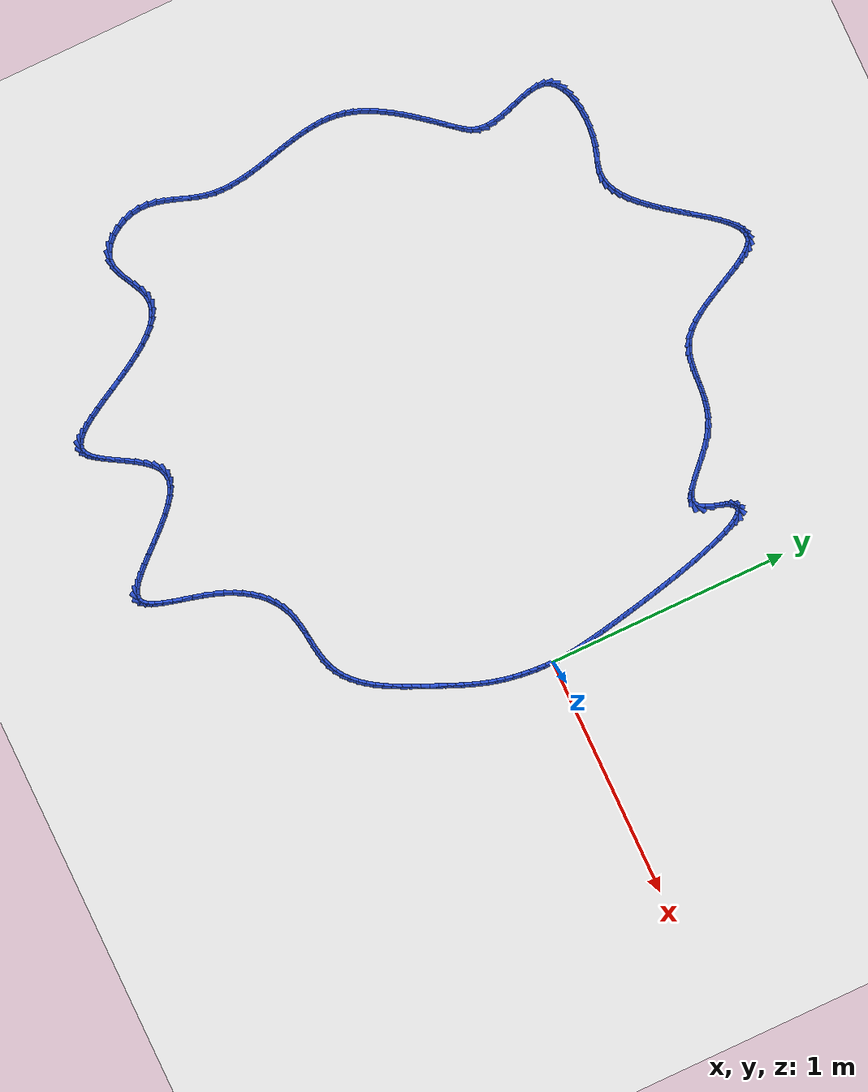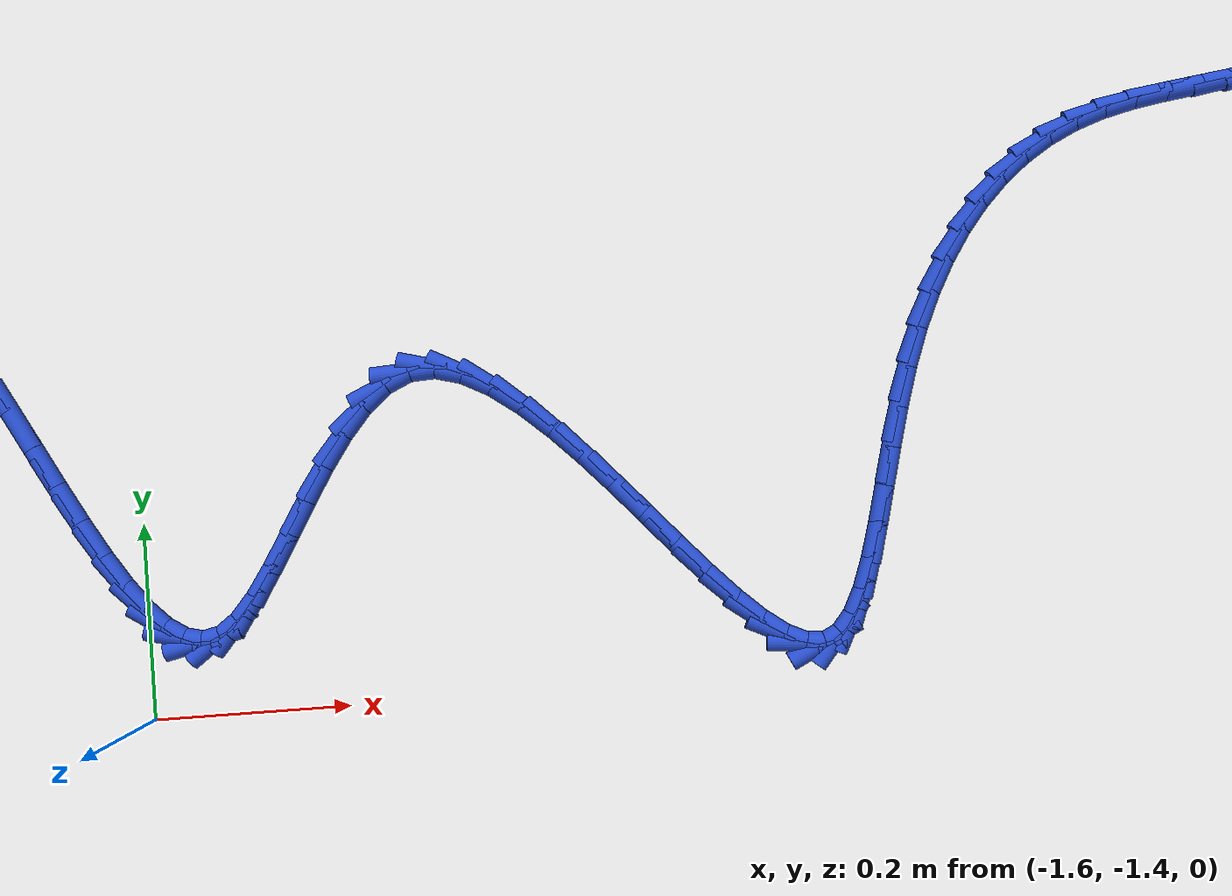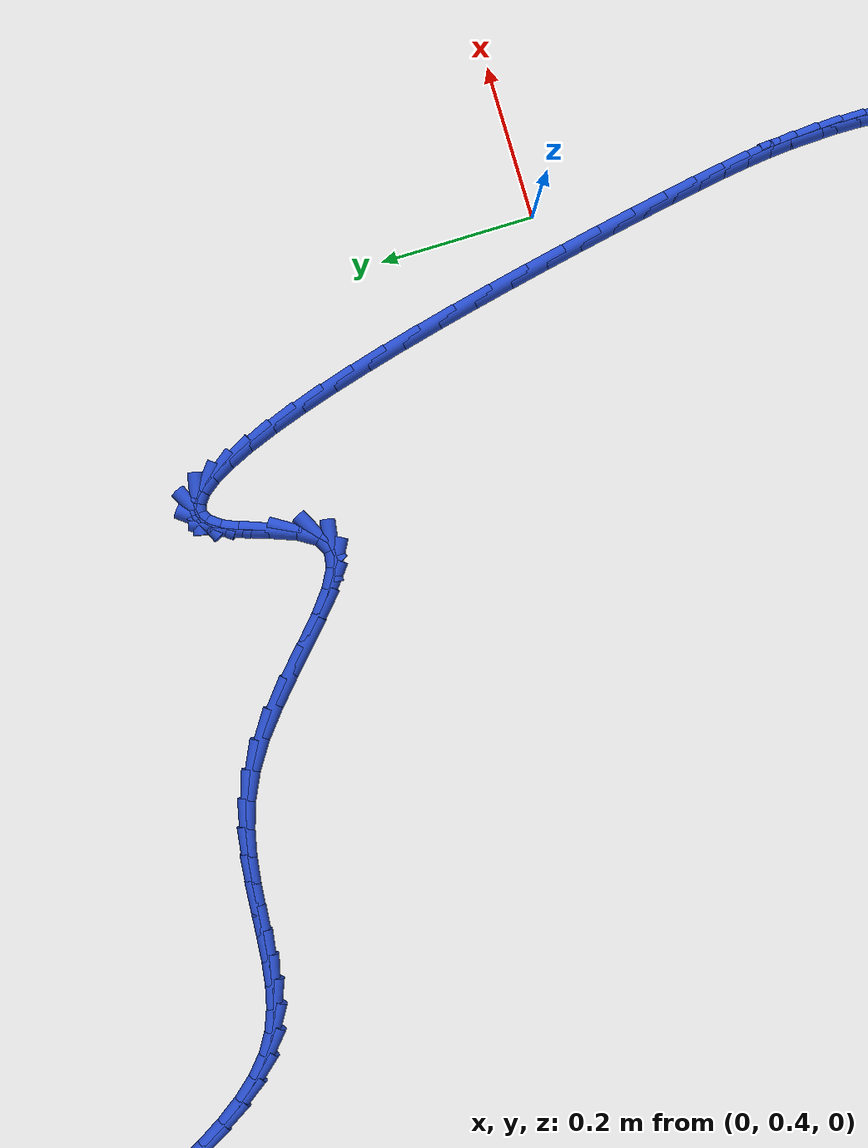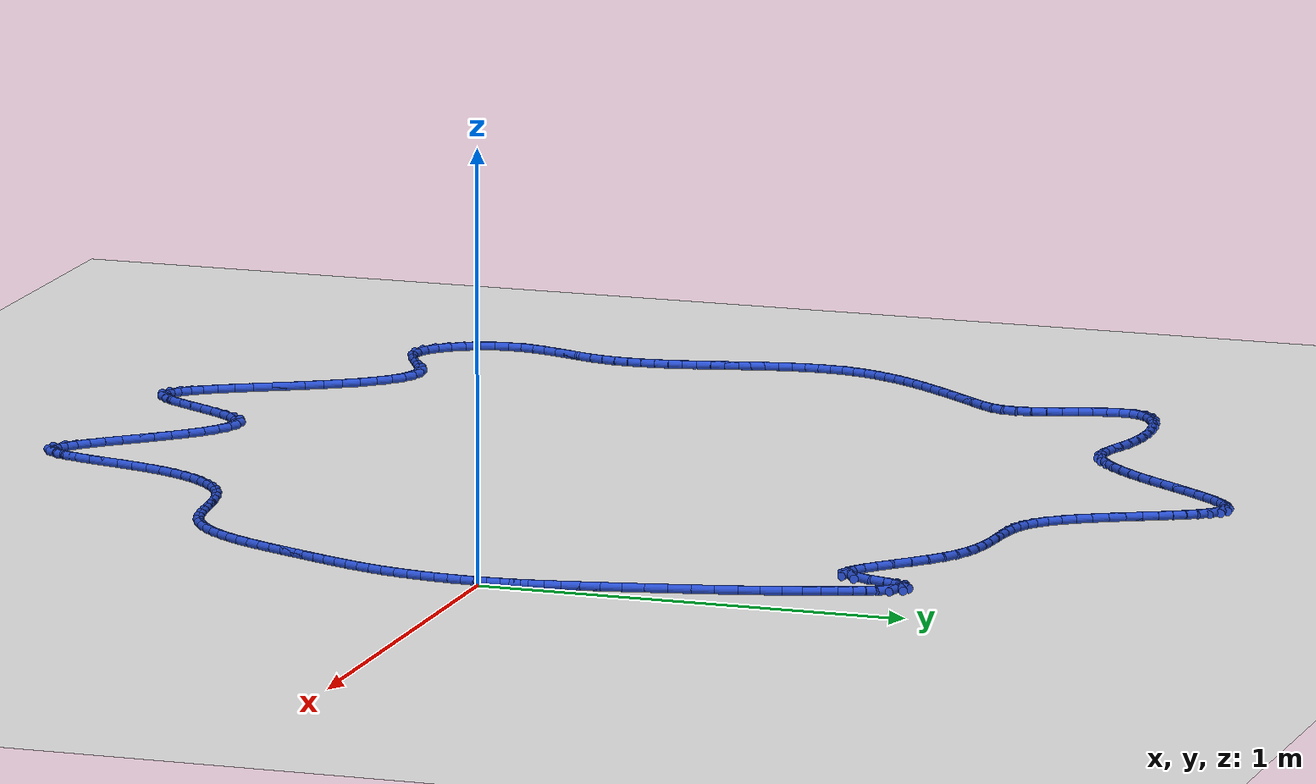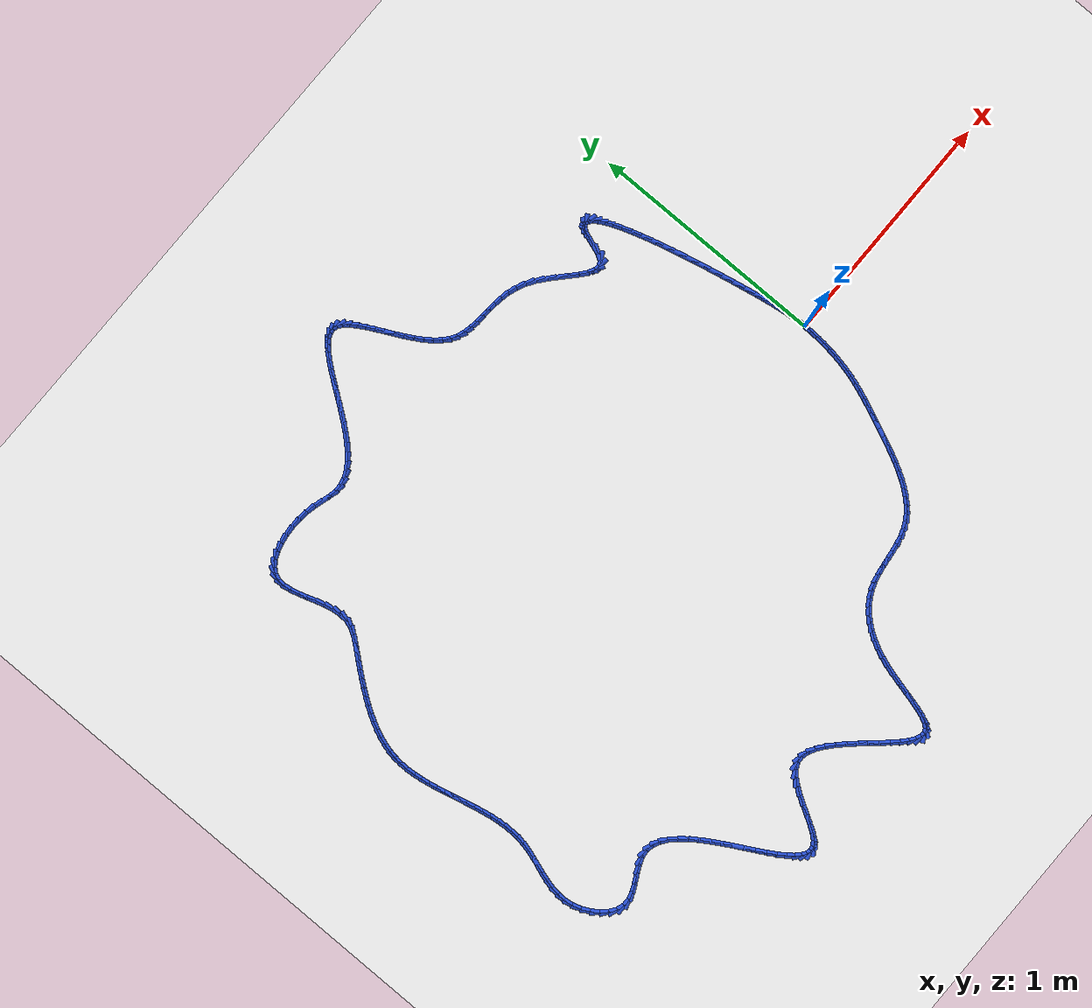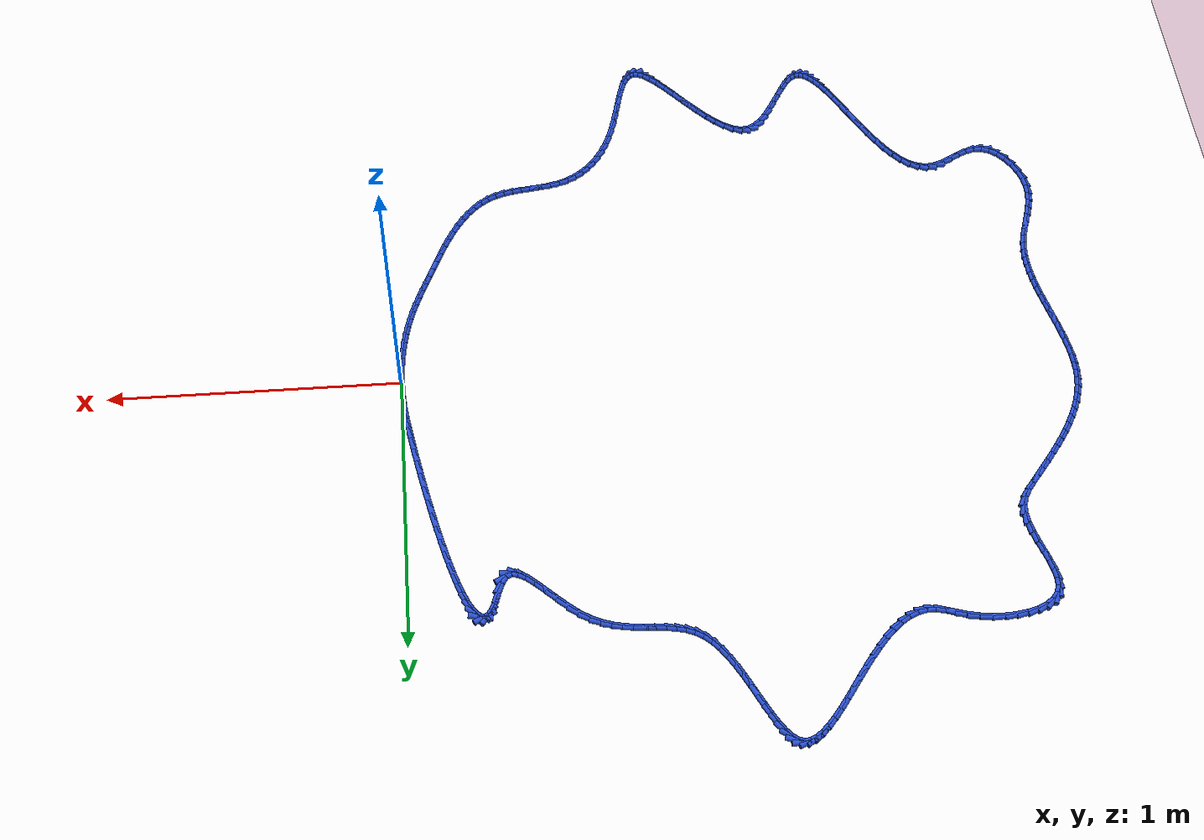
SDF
<sdf version="1.6">
 <world name="default">
  <light name="sun" type="directional">
   <pose>0 0 10 0 -0 0</pose>
   <diffuse>0.8 0.8 0.8 1</diffuse>
   <specular>0.2 0.2 0.2 1</specular>
   <attenuation>
    <range>1000</range>
    <constant>0.9</constant>
    <linear>0.01</linear>
    <quadratic>0.001</quadratic>
   </attenuation>
   <direction>-0.5 0.1 -0.9</direction>
  </light>
  <model name="ground_plane">
   <static>1</static>
   <link name="link">
    <collision name="collision">
     <geometry><plane><normal>0 0 1</normal><size>100 100</size></plane></geometry>
     <surface><friction><ode><mu>100</mu><mu2>50</mu2></ode></friction></surface>
    </collision>
    <visual name="visual">
     <cast_shadows>0</cast_shadows>
     <geometry><plane><normal>0 0 1</normal><size>100 100</size></plane></geometry>
     <material>
      <script><uri>file://media/materials/scripts/gazebo.material</uri><name>Gazebo/WhiteGlow</name></script>
     </material>
    </visual>
   </link>
  </model>
  <gravity>0 0 -9.8</gravity>
  <magnetic_field>6e-06 2.3e-05 -4.2e-05</magnetic_field>
  <atmosphere type="adiabatic"/>
  <physics name="default_physics" default="0" type="ode">
   <max_step_size>0.001</max_step_size>
   <real_time_factor>1</real_time_factor>
   <real_time_update_rate>1000</real_time_update_rate>
  </physics>
  <scene><ambient>0.4 0.4 0.4 1</ambient><background>0.7 0.7 0.7 1</background><shadows>1</shadows></scene>
  <spherical_coordinates>
   <surface_model>EARTH_WGS84</surface_model>
   <latitude_deg>0</latitude_deg>
   <longitude_deg>0</longitude_deg>
   <elevation>0</elevation>
   <heading_deg>0</heading_deg>
  </spherical_coordinates>
  <model name="line">
   <link name="link_0">
    <pose>2.6020852139652106e-18 3.469446951953614e-17 0.01 0 1.57 -1.5464476256501802</pose>
    <collision name="collision">
     <geometry><cylinder><radius>0.01</radius><length>0.08</length></cylinder></geometry>
    </collision>
    <visual name="visual">
     <material>
      <script><name>Gazebo/Blue</name><uri>file://media/materials/scripts/gazebo.material</uri></script>
     </material>
     <geometry><cylinder><radius>0.01</radius><length>0.08</length></cylinder></geometry>
    </visual>
   </link>
   <link name="link_1">
    <pose>-0.0007487655124719422 0.030745686651664664 0.01 0 1.57 -1.5104224034965954</pose>
    <collision name="collision">
     <geometry><cylinder><radius>0.01</radius><length>0.08</length></cylinder></geometry>
    </collision>
    <visual name="visual">
     <material>
      <script><name>Gazebo/Blue</name><uri>file://media/materials/scripts/gazebo.material</uri></script>
     </material>
     <geometry><cylinder><radius>0.01</radius><length>0.08</length></cylinder></geometry>
    </visual>
   </link>
   <link name="link_2">
    <pose>-0.002577657408801142 0.06100161746167763 0.01 0 1.57 -1.4762705760131296</pose>
    <collision name="collision">
     <geometry><cylinder><radius>0.01</radius><length>0.08</length></cylinder></geometry>
    </collision>
    <visual name="visual">
     <material>
      <script><name>Gazebo/Blue</name><uri>file://media/materials/scripts/gazebo.material</uri></script>
     </material>
     <geometry><cylinder><radius>0.01</radius><length>0.08</length></cylinder></geometry>
    </visual>
   </link>
   <link name="link_3">
    <pose>-0.00546558153639707 0.09146228730003628 0.01 0 1.57 -1.4462569014247348</pose>
    <collision name="collision">
     <geometry><cylinder><radius>0.01</radius><length>0.08</length></cylinder></geometry>
    </collision>
    <visual name="visual">
     <material>
      <script><name>Gazebo/Blue</name><uri>file://media/materials/scripts/gazebo.material</uri></script>
     </material>
     <geometry><cylinder><radius>0.01</radius><length>0.08</length></cylinder></geometry>
    </visual>
   </link>
   <link name="link_4">
    <pose>-0.009391443742669208 0.122822191036738 0.01 0 1.57 -1.4219164323984042</pose>
    <collision name="collision">
     <geometry><cylinder><radius>0.01</radius><length>0.08</length></cylinder></geometry>
    </collision>
    <visual name="visual">
     <material>
      <script><name>Gazebo/Blue</name><uri>file://media/materials/scripts/gazebo.material</uri></script>
     </material>
     <geometry><cylinder><radius>0.01</radius><length>0.08</length></cylinder></geometry>
    </visual>
   </link>
   <link name="link_5">
    <pose>-0.014334149875027031 0.15577582354178016 0.01 0 1.57 -1.4038587924622183</pose>
    <collision name="collision">
     <geometry><cylinder><radius>0.01</radius><length>0.08</length></cylinder></geometry>
    </collision>
    <visual name="visual">
     <material>
      <script><name>Gazebo/Blue</name><uri>file://media/materials/scripts/gazebo.material</uri></script>
     </material>
     <geometry><cylinder><radius>0.01</radius><length>0.08</length></cylinder></geometry>
    </visual>
   </link>
   <link name="link_6">
    <pose>-0.02027260578088002 0.19101767968516015 0.01 0 1.57 -1.3918751908380276</pose>
    <collision name="collision">
     <geometry><cylinder><radius>0.01</radius><length>0.08</length></cylinder></geometry>
    </collision>
    <visual name="visual">
     <material>
      <script><name>Gazebo/Blue</name><uri>file://media/materials/scripts/gazebo.material</uri></script>
     </material>
     <geometry><cylinder><radius>0.01</radius><length>0.08</length></cylinder></geometry>
    </visual>
   </link>
   <link name="link_7">
    <pose>-0.027185717307637653 0.22924225433687534 0.01 0 1.57 -1.3848775411903387</pose>
    <collision name="collision">
     <geometry><cylinder><radius>0.01</radius><length>0.08</length></cylinder></geometry>
    </collision>
    <visual name="visual">
     <material>
      <script><name>Gazebo/Blue</name><uri>file://media/materials/scripts/gazebo.material</uri></script>
     </material>
     <geometry><cylinder><radius>0.01</radius><length>0.08</length></cylinder></geometry>
    </visual>
   </link>
   <link name="link_8">
    <pose>-0.03504850345896277 0.27104535770483995 0.01 0 1.57 -1.3791695386713263</pose>
    <collision name="collision">
     <geometry><cylinder><radius>0.01</radius><length>0.08</length></cylinder></geometry>
    </collision>
    <visual name="visual">
     <material>
      <script><name>Gazebo/Blue</name><uri>file://media/materials/scripts/gazebo.material</uri></script>
     </material>
     <geometry><cylinder><radius>0.01</radius><length>0.08</length></cylinder></geometry>
    </visual>
   </link>
   <link name="link_9">
    <pose>-0.04380223645224188 0.31616598906831483 0.01 0 1.57 -1.3729730955867878</pose>
    <collision name="collision">
     <geometry><cylinder><radius>0.01</radius><length>0.08</length></cylinder></geometry>
    </collision>
    <visual name="visual">
     <material>
      <script><name>Gazebo/Blue</name><uri>file://media/materials/scripts/gazebo.material</uri></script>
     </material>
     <geometry><cylinder><radius>0.01</radius><length>0.08</length></cylinder></geometry>
    </visual>
   </link>
   <link name="link_10">
    <pose>-0.05337084768289666 0.36390287450100156 0.01 0 1.57 -1.3660980536907603</pose>
    <collision name="collision">
     <geometry><cylinder><radius>0.01</radius><length>0.08</length></cylinder></geometry>
    </collision>
    <visual name="visual">
     <material>
      <script><name>Gazebo/Blue</name><uri>file://media/materials/scripts/gazebo.material</uri></script>
     </material>
     <geometry><cylinder><radius>0.01</radius><length>0.08</length></cylinder></geometry>
    </visual>
   </link>
   <link name="link_11">
    <pose>-0.06367812628039955 0.413551128028356 0.01 0 1.57 -1.3583442648418198</pose>
    <collision name="collision">
     <geometry><cylinder><radius>0.01</radius><length>0.08</length></cylinder></geometry>
    </collision>
    <visual name="visual">
     <material>
      <script><name>Gazebo/Blue</name><uri>file://media/materials/scripts/gazebo.material</uri></script>
     </material>
     <geometry><cylinder><radius>0.01</radius><length>0.08</length></cylinder></geometry>
    </visual>
   </link>
   <link name="link_12">
    <pose>-0.07464786137422287 0.4644058636758341 0.01 0 1.57 -1.3494669452412287</pose>
    <collision name="collision">
     <geometry><cylinder><radius>0.01</radius><length>0.08</length></cylinder></geometry>
    </collision>
    <visual name="visual">
     <material>
      <script><name>Gazebo/Blue</name><uri>file://media/materials/scripts/gazebo.material</uri></script>
     </material>
     <geometry><cylinder><radius>0.01</radius><length>0.08</length></cylinder></geometry>
    </visual>
   </link>
   <link name="link_13">
    <pose>-0.08620384209383913 0.5157621954688922 0.01 0 1.57 -1.3391499191216563</pose>
    <collision name="collision">
     <geometry><cylinder><radius>0.01</radius><length>0.08</length></cylinder></geometry>
    </collision>
    <visual name="visual">
     <material>
      <script><name>Gazebo/Blue</name><uri>file://media/materials/scripts/gazebo.material</uri></script>
     </material>
     <geometry><cylinder><radius>0.01</radius><length>0.08</length></cylinder></geometry>
    </visual>
   </link>
   <link name="link_14">
    <pose>-0.09826985756872064 0.5669152374329861 0.01 0 1.57 -1.3269676983986676</pose>
    <collision name="collision">
     <geometry><cylinder><radius>0.01</radius><length>0.08</length></cylinder></geometry>
    </collision>
    <visual name="visual">
     <material>
      <script><name>Gazebo/Blue</name><uri>file://media/materials/scripts/gazebo.material</uri></script>
     </material>
     <geometry><cylinder><radius>0.01</radius><length>0.08</length></cylinder></geometry>
    </visual>
   </link>
   <link name="link_15">
    <pose>-0.1107696969283398 0.6171601035935718 0.01 0 1.57 -1.312326621351807</pose>
    <collision name="collision">
     <geometry><cylinder><radius>0.01</radius><length>0.08</length></cylinder></geometry>
    </collision>
    <visual name="visual">
     <material>
      <script><name>Gazebo/Blue</name><uri>file://media/materials/scripts/gazebo.material</uri></script>
     </material>
     <geometry><cylinder><radius>0.01</radius><length>0.08</length></cylinder></geometry>
    </visual>
   </link>
   <link name="link_16">
    <pose>-0.12362714930216906 0.6657919079761055 0.01 0 1.57 -1.294367646955937</pose>
    <collision name="collision">
     <geometry><cylinder><radius>0.01</radius><length>0.08</length></cylinder></geometry>
    </collision>
    <visual name="visual">
     <material>
      <script><name>Gazebo/Blue</name><uri>file://media/materials/scripts/gazebo.material</uri></script>
     </material>
     <geometry><cylinder><radius>0.01</radius><length>0.08</length></cylinder></geometry>
    </visual>
   </link>
   <link name="link_17">
    <pose>-0.13676600381968082 0.7121057646060435 0.01 0 1.57 -1.2717967072354575</pose>
    <collision name="collision">
     <geometry><cylinder><radius>0.01</radius><length>0.08</length></cylinder></geometry>
    </collision>
    <visual name="visual">
     <material>
      <script><name>Gazebo/Blue</name><uri>file://media/materials/scripts/gazebo.material</uri></script>
     </material>
     <geometry><cylinder><radius>0.01</radius><length>0.08</length></cylinder></geometry>
    </visual>
   </link>
   <link name="link_18">
    <pose>-0.15011004961034738 0.7553967875088409 0.01 0 1.57 -1.2425707087678826</pose>
    <collision name="collision">
     <geometry><cylinder><radius>0.01</radius><length>0.08</length></cylinder></geometry>
    </collision>
    <visual name="visual">
     <material>
      <script><name>Gazebo/Blue</name><uri>file://media/materials/scripts/gazebo.material</uri></script>
     </material>
     <geometry><cylinder><radius>0.01</radius><length>0.08</length></cylinder></geometry>
    </visual>
   </link>
   <link name="link_19">
    <pose>-0.16358307580364123 0.7949600907099548 0.01 0 1.57 -1.2032756551532462</pose>
    <collision name="collision">
     <geometry><cylinder><radius>0.01</radius><length>0.08</length></cylinder></geometry>
    </collision>
    <visual name="visual">
     <material>
      <script><name>Gazebo/Blue</name><uri>file://media/materials/scripts/gazebo.material</uri></script>
     </material>
     <geometry><cylinder><radius>0.01</radius><length>0.08</length></cylinder></geometry>
    </visual>
   </link>
   <link name="link_20">
    <pose>-0.1771088715290347 0.8300907882348404 0.01 0 1.57 -1.1477923631294051</pose>
    <collision name="collision">
     <geometry><cylinder><radius>0.01</radius><length>0.08</length></cylinder></geometry>
    </collision>
    <visual name="visual">
     <material>
      <script><name>Gazebo/Blue</name><uri>file://media/materials/scripts/gazebo.material</uri></script>
     </material>
     <geometry><cylinder><radius>0.01</radius><length>0.08</length></cylinder></geometry>
    </visual>
   </link>
   <link name="link_21">
    <pose>-0.1906112259160003 0.8600839941089542 0.01 0 1.57 -1.0641543445120567</pose>
    <collision name="collision">
     <geometry><cylinder><radius>0.01</radius><length>0.08</length></cylinder></geometry>
    </collision>
    <visual name="visual">
     <material>
      <script><name>Gazebo/Blue</name><uri>file://media/materials/scripts/gazebo.material</uri></script>
     </material>
     <geometry><cylinder><radius>0.01</radius><length>0.08</length></cylinder></geometry>
    </visual>
   </link>
   <link name="link_22">
    <pose>-0.2040139280940103 0.8842348223577521 0.01 0 1.57 -0.9264172251843087</pose>
    <collision name="collision">
     <geometry><cylinder><radius>0.01</radius><length>0.08</length></cylinder></geometry>
    </collision>
    <visual name="visual">
     <material>
      <script><name>Gazebo/Blue</name><uri>file://media/materials/scripts/gazebo.material</uri></script>
     </material>
     <geometry><cylinder><radius>0.01</radius><length>0.08</length></cylinder></geometry>
    </visual>
   </link>
   <link name="link_23">
    <pose>-0.21724076719253713 0.9018383870066901 0.01 0 1.57 -0.6734049822729485</pose>
    <collision name="collision">
     <geometry><cylinder><radius>0.01</radius><length>0.08</length></cylinder></geometry>
    </collision>
    <visual name="visual">
     <material>
      <script><name>Gazebo/Blue</name><uri>file://media/materials/scripts/gazebo.material</uri></script>
     </material>
     <geometry><cylinder><radius>0.01</radius><length>0.08</length></cylinder></geometry>
    </visual>
   </link>
   <link name="link_24">
    <pose>-0.23021553234105324 0.9121898020812245 0.01 0 1.57 -0.18711684541497944</pose>
    <collision name="collision">
     <geometry><cylinder><radius>0.01</radius><length>0.08</length></cylinder></geometry>
    </collision>
    <visual name="visual">
     <material>
      <script><name>Gazebo/Blue</name><uri>file://media/materials/scripts/gazebo.material</uri></script>
     </material>
     <geometry><cylinder><radius>0.01</radius><length>0.08</length></cylinder></geometry>
    </visual>
   </link>
   <link name="link_25">
    <pose>-0.2428620126690309 0.9145841816068108 0.01 0 1.57 0.47317853843520746</pose>
    <collision name="collision">
     <geometry><cylinder><radius>0.01</radius><length>0.08</length></cylinder></geometry>
    </collision>
    <visual name="visual">
     <material>
      <script><name>Gazebo/Blue</name><uri>file://media/materials/scripts/gazebo.material</uri></script>
     </material>
     <geometry><cylinder><radius>0.01</radius><length>0.08</length></cylinder></geometry>
    </visual>
   </link>
   <link name="link_26">
    <pose>-0.2551039973059427 0.9083166396089053 0.01 0 1.57 0.92584293908052</pose>
    <collision name="collision">
     <geometry><cylinder><radius>0.01</radius><length>0.08</length></cylinder></geometry>
    </collision>
    <visual name="visual">
     <material>
      <script><name>Gazebo/Blue</name><uri>file://media/materials/scripts/gazebo.material</uri></script>
     </material>
     <geometry><cylinder><radius>0.01</radius><length>0.08</length></cylinder></geometry>
    </visual>
   </link>
   <link name="link_27">
    <pose>-0.26686527538126087 0.8926822901129643 0.01 0 1.57 1.1592164706450918</pose>
    <collision name="collision">
     <geometry><cylinder><radius>0.01</radius><length>0.08</length></cylinder></geometry>
    </collision>
    <visual name="visual">
     <material>
      <script><name>Gazebo/Blue</name><uri>file://media/materials/scripts/gazebo.material</uri></script>
     </material>
     <geometry><cylinder><radius>0.01</radius><length>0.08</length></cylinder></geometry>
    </visual>
   </link>
   <link name="link_28">
    <pose>-0.27807422056377834 0.8670037838245043 0.01 0 1.57 1.2503655635150068</pose>
    <collision name="collision">
     <geometry><cylinder><radius>0.01</radius><length>0.08</length></cylinder></geometry>
    </collision>
    <visual name="visual">
     <material>
      <script><name>Gazebo/Blue</name><uri>file://media/materials/scripts/gazebo.material</uri></script>
     </material>
     <geometry><cylinder><radius>0.01</radius><length>0.08</length></cylinder></geometry>
    </visual>
   </link>
   <link name="link_29">
    <pose>-0.2891586480716466 0.8336036284013868 0.01 0 1.57 1.2146622342306626</pose>
    <collision name="collision">
     <geometry><cylinder><radius>0.01</radius><length>0.08</length></cylinder></geometry>
    </collision>
    <visual name="visual">
     <material>
      <script><name>Gazebo/Blue</name><uri>file://media/materials/scripts/gazebo.material</uri></script>
     </material>
     <geometry><cylinder><radius>0.01</radius><length>0.08</length></cylinder></geometry>
    </visual>
   </link>
   <link name="link_30">
    <pose>-0.30148796301030795 0.800459918172773 0.01 0 1.57 1.0161993722876308</pose>
    <collision name="collision">
     <geometry><cylinder><radius>0.01</radius><length>0.08</length></cylinder></geometry>
    </collision>
    <visual name="visual">
     <material>
      <script><name>Gazebo/Blue</name><uri>file://media/materials/scripts/gazebo.material</uri></script>
     </material>
     <geometry><cylinder><radius>0.01</radius><length>0.08</length></cylinder></geometry>
    </visual>
   </link>
   <link name="link_31">
    <pose>-0.3165345752909794 0.7761695653891478 0.01 0 1.57 0.4786452891999219</pose>
    <collision name="collision">
     <geometry><cylinder><radius>0.01</radius><length>0.08</length></cylinder></geometry>
    </collision>
    <visual name="visual">
     <material>
      <script><name>Gazebo/Blue</name><uri>file://media/materials/scripts/gazebo.material</uri></script>
     </material>
     <geometry><cylinder><radius>0.01</radius><length>0.08</length></cylinder></geometry>
    </visual>
   </link>
   <link name="link_32">
    <pose>-0.3352822161873972 0.7664415987991907 0.01 0 1.57 -0.14962059238042957</pose>
    <collision name="collision">
     <geometry><cylinder><radius>0.01</radius><length>0.08</length></cylinder></geometry>
    </collision>
    <visual name="visual">
     <material>
      <script><name>Gazebo/Blue</name><uri>file://media/materials/scripts/gazebo.material</uri></script>
     </material>
     <geometry><cylinder><radius>0.01</radius><length>0.08</length></cylinder></geometry>
    </visual>
   </link>
   <link name="link_33">
    <pose>-0.3574971679656393 0.769790439829212 0.01 0 1.57 -0.5011459220433687</pose>
    <collision name="collision">
     <geometry><cylinder><radius>0.01</radius><length>0.08</length></cylinder></geometry>
    </collision>
    <visual name="visual">
     <material>
      <script><name>Gazebo/Blue</name><uri>file://media/materials/scripts/gazebo.material</uri></script>
     </material>
     <geometry><cylinder><radius>0.01</radius><length>0.08</length></cylinder></geometry>
    </visual>
   </link>
   <link name="link_34">
    <pose>-0.3827592866161876 0.7836288096790219 0.01 0 1.57 -0.6621384136848523</pose>
    <collision name="collision">
     <geometry><cylinder><radius>0.01</radius><length>0.08</length></cylinder></geometry>
    </collision>
    <visual name="visual">
     <material>
      <script><name>Gazebo/Blue</name><uri>file://media/materials/scripts/gazebo.material</uri></script>
     </material>
     <geometry><cylinder><radius>0.01</radius><length>0.08</length></cylinder></geometry>
    </visual>
   </link>
   <link name="link_35">
    <pose>-0.4106484281295235 0.8053694295484323 0.01 0 1.57 -0.7322489039355877</pose>
    <collision name="collision">
     <geometry><cylinder><radius>0.01</radius><length>0.08</length></cylinder></geometry>
    </collision>
    <visual name="visual">
     <material>
      <script><name>Gazebo/Blue</name><uri>file://media/materials/scripts/gazebo.material</uri></script>
     </material>
     <geometry><cylinder><radius>0.01</radius><length>0.08</length></cylinder></geometry>
    </visual>
   </link>
   <link name="link_36">
    <pose>-0.4407444484961283 0.8324250206372528 0.01 0 1.57 -0.7513654748937402</pose>
    <collision name="collision">
     <geometry><cylinder><radius>0.01</radius><length>0.08</length></cylinder></geometry>
    </collision>
    <visual name="visual">
     <material>
      <script><name>Gazebo/Blue</name><uri>file://media/materials/scripts/gazebo.material</uri></script>
     </material>
     <geometry><cylinder><radius>0.01</radius><length>0.08</length></cylinder></geometry>
    </visual>
   </link>
   <link name="link_37">
    <pose>-0.472627203706484 0.8622083041452955 0.01 0 1.57 -0.7328032323105936</pose>
    <collision name="collision">
     <geometry><cylinder><radius>0.01</radius><length>0.08</length></cylinder></geometry>
    </collision>
    <visual name="visual">
     <material>
      <script><name>Gazebo/Blue</name><uri>file://media/materials/scripts/gazebo.material</uri></script>
     </material>
     <geometry><cylinder><radius>0.01</radius><length>0.08</length></cylinder></geometry>
    </visual>
   </link>
   <link name="link_38">
    <pose>-0.5058765497510723 0.8921320012723709 0.01 0 1.57 -0.6768805529917868</pose>
    <collision name="collision">
     <geometry><cylinder><radius>0.01</radius><length>0.08</length></cylinder></geometry>
    </collision>
    <visual name="visual">
     <material>
      <script><name>Gazebo/Blue</name><uri>file://media/materials/scripts/gazebo.material</uri></script>
     </material>
     <geometry><cylinder><radius>0.01</radius><length>0.08</length></cylinder></geometry>
    </visual>
   </link>
   <link name="link_39">
    <pose>-0.5400723426203746 0.91960883321829 0.01 0 1.57 -0.5746531600312526</pose>
    <collision name="collision">
     <geometry><cylinder><radius>0.01</radius><length>0.08</length></cylinder></geometry>
    </collision>
    <visual name="visual">
     <material>
      <script><name>Gazebo/Blue</name><uri>file://media/materials/scripts/gazebo.material</uri></script>
     </material>
     <geometry><cylinder><radius>0.01</radius><length>0.08</length></cylinder></geometry>
    </visual>
   </link>
   <link name="link_40">
    <pose>-0.5747970883728617 0.942094950162464 0.01 0 1.57 -0.4415338205154128</pose>
    <collision name="collision">
     <geometry><cylinder><radius>0.01</radius><length>0.08</length></cylinder></geometry>
    </collision>
    <visual name="visual">
     <material>
      <script><name>Gazebo/Blue</name><uri>file://media/materials/scripts/gazebo.material</uri></script>
     </material>
     <geometry><cylinder><radius>0.01</radius><length>0.08</length></cylinder></geometry>
    </visual>
   </link>
   <link name="link_41">
    <pose>-0.6097284206902308 0.9586054417624702 0.01 0 1.57 -0.3180967803701681</pose>
    <collision name="collision">
     <geometry><cylinder><radius>0.01</radius><length>0.08</length></cylinder></geometry>
    </collision>
    <visual name="visual">
     <material>
      <script><name>Gazebo/Blue</name><uri>file://media/materials/scripts/gazebo.material</uri></script>
     </material>
     <geometry><cylinder><radius>0.01</radius><length>0.08</length></cylinder></geometry>
    </visual>
   </link>
   <link name="link_42">
    <pose>-0.6446631653225249 0.97010870224219 0.01 0 1.57 -0.21502965447356776</pose>
    <collision name="collision">
     <geometry><cylinder><radius>0.01</radius><length>0.08</length></cylinder></geometry>
    </collision>
    <visual name="visual">
     <material>
      <script><name>Gazebo/Blue</name><uri>file://media/materials/scripts/gazebo.material</uri></script>
     </material>
     <geometry><cylinder><radius>0.01</radius><length>0.08</length></cylinder></geometry>
    </visual>
   </link>
   <link name="link_43">
    <pose>-0.6794056878377567 0.9776966874103797 0.01 0 1.57 -0.13781138018168332</pose>
    <collision name="collision">
     <geometry><cylinder><radius>0.01</radius><length>0.08</length></cylinder></geometry>
    </collision>
    <visual name="visual">
     <material>
      <script><name>Gazebo/Blue</name><uri>file://media/materials/scripts/gazebo.material</uri></script>
     </material>
     <geometry><cylinder><radius>0.01</radius><length>0.08</length></cylinder></geometry>
    </visual>
   </link>
   <link name="link_44">
    <pose>-0.7137603538039384 0.9824613530757954 0.01 0 1.57 -0.0895788842612445</pose>
    <collision name="collision">
     <geometry><cylinder><radius>0.01</radius><length>0.08</length></cylinder></geometry>
    </collision>
    <visual name="visual">
     <material>
      <script><name>Gazebo/Blue</name><uri>file://media/materials/scripts/gazebo.material</uri></script>
     </material>
     <geometry><cylinder><radius>0.01</radius><length>0.08</length></cylinder></geometry>
    </visual>
   </link>
   <link name="link_45">
    <pose>-0.747531528789083 0.9854946550471931 0.01 0 1.57 -0.07243278679098339</pose>
    <collision name="collision">
     <geometry><cylinder><radius>0.01</radius><length>0.08</length></cylinder></geometry>
    </collision>
    <visual name="visual">
     <material>
      <script><name>Gazebo/Blue</name><uri>file://media/materials/scripts/gazebo.material</uri></script>
     </material>
     <geometry><cylinder><radius>0.01</radius><length>0.08</length></cylinder></geometry>
    </visual>
   </link>
   <link name="link_46">
    <pose>-0.7805235783612035 0.9878885491333294 0.01 0 1.57 -0.08867015816660742</pose>
    <collision name="collision">
     <geometry><cylinder><radius>0.01</radius><length>0.08</length></cylinder></geometry>
    </collision>
    <visual name="visual">
     <material>
      <script><name>Gazebo/Blue</name><uri>file://media/materials/scripts/gazebo.material</uri></script>
     </material>
     <geometry><cylinder><radius>0.01</radius><length>0.08</length></cylinder></geometry>
    </visual>
   </link>
   <link name="link_47">
    <pose>-0.8125408680883122 0.9907349911429598 0.01 0 1.57 -0.1413965297258001</pose>
    <collision name="collision">
     <geometry><cylinder><radius>0.01</radius><length>0.08</length></cylinder></geometry>
    </collision>
    <visual name="visual">
     <material>
      <script><name>Gazebo/Blue</name><uri>file://media/materials/scripts/gazebo.material</uri></script>
     </material>
     <geometry><cylinder><radius>0.01</radius><length>0.08</length></cylinder></geometry>
    </visual>
   </link>
   <link name="link_48">
    <pose>-0.8433877635384216 0.9951259368848406 0.01 0 1.57 -0.23400482564709438</pose>
    <collision name="collision">
     <geometry><cylinder><radius>0.01</radius><length>0.08</length></cylinder></geometry>
    </collision>
    <visual name="visual">
     <material>
      <script><name>Gazebo/Blue</name><uri>file://media/materials/scripts/gazebo.material</uri></script>
     </material>
     <geometry><cylinder><radius>0.01</radius><length>0.08</length></cylinder></geometry>
    </visual>
   </link>
   <link name="link_49">
    <pose>-0.8728686302795443 1.0021533421677278 0.01 0 1.57 -0.3677249121886853</pose>
    <collision name="collision">
     <geometry><cylinder><radius>0.01</radius><length>0.08</length></cylinder></geometry>
    </collision>
    <visual name="visual">
     <material>
      <script><name>Gazebo/Blue</name><uri>file://media/materials/scripts/gazebo.material</uri></script>
     </material>
     <geometry><cylinder><radius>0.01</radius><length>0.08</length></cylinder></geometry>
    </visual>
   </link>
   <link name="link_50">
    <pose>-0.9007878338796937 1.012909162800378 0.01 0 1.57 -0.5369145037270657</pose>
    <collision name="collision">
     <geometry><cylinder><radius>0.01</radius><length>0.08</length></cylinder></geometry>
    </collision>
    <visual name="visual">
     <material>
      <script><name>Gazebo/Blue</name><uri>file://media/materials/scripts/gazebo.material</uri></script>
     </material>
     <geometry><cylinder><radius>0.01</radius><length>0.08</length></cylinder></geometry>
    </visual>
   </link>
   <link name="link_51">
    <pose>-0.9269504467968548 1.0284822799401567 0.01 0 1.57 -0.7104099477571018</pose>
    <collision name="collision">
     <geometry><cylinder><radius>0.01</radius><length>0.08</length></cylinder></geometry>
    </collision>
    <visual name="visual">
     <material>
      <script><name>Gazebo/Blue</name><uri>file://media/materials/scripts/gazebo.material</uri></script>
     </material>
     <geometry><cylinder><radius>0.01</radius><length>0.08</length></cylinder></geometry>
    </visual>
   </link>
   <link name="link_52">
    <pose>-0.9512866714759047 1.04941731594464 0.01 0 1.57 -0.8466700879214839</pose>
    <collision name="collision">
     <geometry><cylinder><radius>0.01</radius><length>0.08</length></cylinder></geometry>
    </collision>
    <visual name="visual">
     <material>
      <script><name>Gazebo/Blue</name><uri>file://media/materials/scripts/gazebo.material</uri></script>
     </material>
     <geometry><cylinder><radius>0.01</radius><length>0.08</length></cylinder></geometry>
    </visual>
   </link>
   <link name="link_53">
    <pose>-0.9739946262250186 1.0750935804448265 0.01 0 1.57 -0.9473832392303342</pose>
    <collision name="collision">
     <geometry><cylinder><radius>0.01</radius><length>0.08</length></cylinder></geometry>
    </collision>
    <visual name="visual">
     <material>
      <script><name>Gazebo/Blue</name><uri>file://media/materials/scripts/gazebo.material</uri></script>
     </material>
     <geometry><cylinder><radius>0.01</radius><length>0.08</length></cylinder></geometry>
    </visual>
   </link>
   <link name="link_54">
    <pose>-0.9953051708603469 1.1047296647303828 0.01 0 1.57 -1.0188137581662418</pose>
    <collision name="collision">
     <geometry><cylinder><radius>0.01</radius><length>0.08</length></cylinder></geometry>
    </collision>
    <visual name="visual">
     <material>
      <script><name>Gazebo/Blue</name><uri>file://media/materials/scripts/gazebo.material</uri></script>
     </material>
     <geometry><cylinder><radius>0.01</radius><length>0.08</length></cylinder></geometry>
    </visual>
   </link>
   <link name="link_55">
    <pose>-1.0154234042542682 1.1373978133899758 0.01 0 1.57 -1.0669198641161672</pose>
    <collision name="collision">
     <geometry><cylinder><radius>0.01</radius><length>0.08</length></cylinder></geometry>
    </collision>
    <visual name="visual">
     <material>
      <script><name>Gazebo/Blue</name><uri>file://media/materials/scripts/gazebo.material</uri></script>
     </material>
     <geometry><cylinder><radius>0.01</radius><length>0.08</length></cylinder></geometry>
    </visual>
   </link>
   <link name="link_56">
    <pose>-1.0345353581518941 1.172061951565698 0.01 0 1.57 -1.0964157012653144</pose>
    <collision name="collision">
     <geometry><cylinder><radius>0.01</radius><length>0.08</length></cylinder></geometry>
    </collision>
    <visual name="visual">
     <material>
      <script><name>Gazebo/Blue</name><uri>file://media/materials/scripts/gazebo.material</uri></script>
     </material>
     <geometry><cylinder><radius>0.01</radius><length>0.08</length></cylinder></geometry>
    </visual>
   </link>
   <link name="link_57">
    <pose>-1.05282661597951 1.2076834575216233 0.01 0 1.57 -1.1097176803708253</pose>
    <collision name="collision">
     <geometry><cylinder><radius>0.01</radius><length>0.08</length></cylinder></geometry>
    </collision>
    <visual name="visual">
     <material>
      <script><name>Gazebo/Blue</name><uri>file://media/materials/scripts/gazebo.material</uri></script>
     </material>
     <geometry><cylinder><radius>0.01</radius><length>0.08</length></cylinder></geometry>
    </visual>
   </link>
   <link name="link_58">
    <pose>-1.0704827611633996 1.2432237095218246 0.01 0 1.57 -1.1072317461975751</pose>
    <collision name="collision">
     <geometry><cylinder><radius>0.01</radius><length>0.08</length></cylinder></geometry>
    </collision>
    <visual name="visual">
     <material>
      <script><name>Gazebo/Blue</name><uri>file://media/materials/scripts/gazebo.material</uri></script>
     </material>
     <geometry><cylinder><radius>0.01</radius><length>0.08</length></cylinder></geometry>
    </visual>
   </link>
   <link name="link_59">
    <pose>-1.087689377129848 1.2776440858303753 0.01 0 1.57 -1.087223373618693</pose>
    <collision name="collision">
     <geometry><cylinder><radius>0.01</radius><length>0.08</length></cylinder></geometry>
    </collision>
    <visual name="visual">
     <material>
      <script><name>Gazebo/Blue</name><uri>file://media/materials/scripts/gazebo.material</uri></script>
     </material>
     <geometry><cylinder><radius>0.01</radius><length>0.08</length></cylinder></geometry>
    </visual>
   </link>
   <link name="link_60">
    <pose>-1.1046320473051392 1.3099059647113473 0.01 0 1.57 -1.045038843182459</pose>
    <collision name="collision">
     <geometry><cylinder><radius>0.01</radius><length>0.08</length></cylinder></geometry>
    </collision>
    <visual name="visual">
     <material>
      <script><name>Gazebo/Blue</name><uri>file://media/materials/scripts/gazebo.material</uri></script>
     </material>
     <geometry><cylinder><radius>0.01</radius><length>0.08</length></cylinder></geometry>
    </visual>
   </link>
   <link name="link_61">
    <pose>-1.121496355115558 1.3389707244288145 0.01 0 1.57 -0.9712056810881692</pose>
    <collision name="collision">
     <geometry><cylinder><radius>0.01</radius><length>0.08</length></cylinder></geometry>
    </collision>
    <visual name="visual">
     <material>
      <script><name>Gazebo/Blue</name><uri>file://media/materials/scripts/gazebo.material</uri></script>
     </material>
     <geometry><cylinder><radius>0.01</radius><length>0.08</length></cylinder></geometry>
    </visual>
   </link>
   <link name="link_62">
    <pose>-1.1384678839873892 1.3637997432468505 0.01 0 1.57 -0.8475230503554604</pose>
    <collision name="collision">
     <geometry><cylinder><radius>0.01</radius><length>0.08</length></cylinder></geometry>
    </collision>
    <visual name="visual">
     <material>
      <script><name>Gazebo/Blue</name><uri>file://media/materials/scripts/gazebo.material</uri></script>
     </material>
     <geometry><cylinder><radius>0.01</radius><length>0.08</length></cylinder></geometry>
    </visual>
   </link>
   <link name="link_63">
    <pose>-1.1557322173469164 1.3833543994295272 0.01 0 1.57 -0.6411389970311895</pose>
    <collision name="collision">
     <geometry><cylinder><radius>0.01</radius><length>0.08</length></cylinder></geometry>
    </collision>
    <visual name="visual">
     <material>
      <script><name>Gazebo/Blue</name><uri>file://media/materials/scripts/gazebo.material</uri></script>
     </material>
     <geometry><cylinder><radius>0.01</radius><length>0.08</length></cylinder></geometry>
    </visual>
   </link>
   <link name="link_64">
    <pose>-1.173474938620425 1.396596071240918 0.01 0 1.57 -0.3102830415992613</pose>
    <collision name="collision">
     <geometry><cylinder><radius>0.01</radius><length>0.08</length></cylinder></geometry>
    </collision>
    <visual name="visual">
     <material>
      <script><name>Gazebo/Blue</name><uri>file://media/materials/scripts/gazebo.material</uri></script>
     </material>
     <geometry><cylinder><radius>0.01</radius><length>0.08</length></cylinder></geometry>
    </visual>
   </link>
   <link name="link_65">
    <pose>-1.1918803715735002 1.4024975822284373 0.01 0 1.57 0.0923245389611452</pose>
    <collision name="collision">
     <geometry><cylinder><radius>0.01</radius><length>0.08</length></cylinder></geometry>
    </collision>
    <visual name="visual">
     <material>
      <script><name>Gazebo/Blue</name><uri>file://media/materials/scripts/gazebo.material</uri></script>
     </material>
     <geometry><cylinder><radius>0.01</radius><length>0.08</length></cylinder></geometry>
    </visual>
   </link>
   <link name="link_66">
    <pose>-1.2110568640180306 1.4007220738306414 0.01 0 1.57 0.41217816165233906</pose>
    <collision name="collision">
     <geometry><cylinder><radius>0.01</radius><length>0.08</length></cylinder></geometry>
    </collision>
    <visual name="visual">
     <material>
      <script><name>Gazebo/Blue</name><uri>file://media/materials/scripts/gazebo.material</uri></script>
     </material>
     <geometry><cylinder><radius>0.01</radius><length>0.08</length></cylinder></geometry>
    </visual>
   </link>
   <link name="link_67">
    <pose>-1.2309947725913668 1.3920047558816475 0.01 0 1.57 0.6221801606541436</pose>
    <collision name="collision">
     <geometry><cylinder><radius>0.01</radius><length>0.08</length></cylinder></geometry>
    </collision>
    <visual name="visual">
     <material>
      <script><name>Gazebo/Blue</name><uri>file://media/materials/scripts/gazebo.material</uri></script>
     </material>
     <geometry><cylinder><radius>0.01</radius><length>0.08</length></cylinder></geometry>
    </visual>
   </link>
   <link name="link_68">
    <pose>-1.2516742774052378 1.3771733021776984 0.01 0 1.57 0.7544978303005261</pose>
    <collision name="collision">
     <geometry><cylinder><radius>0.01</radius><length>0.08</length></cylinder></geometry>
    </collision>
    <visual name="visual">
     <material>
      <script><name>Gazebo/Blue</name><uri>file://media/materials/scripts/gazebo.material</uri></script>
     </material>
     <geometry><cylinder><radius>0.01</radius><length>0.08</length></cylinder></geometry>
    </visual>
   </link>
   <link name="link_69">
    <pose>-1.2730755585713744 1.3570553865150368 0.01 0 1.57 0.8383364295871951</pose>
    <collision name="collision">
     <geometry><cylinder><radius>0.01</radius><length>0.08</length></cylinder></geometry>
    </collision>
    <visual name="visual">
     <material>
      <script><name>Gazebo/Blue</name><uri>file://media/materials/scripts/gazebo.material</uri></script>
     </material>
     <geometry><cylinder><radius>0.01</radius><length>0.08</length></cylinder></geometry>
    </visual>
   </link>
   <link name="link_70">
    <pose>-1.2951787962015062 1.3324786826899055 0.01 0 1.57 0.89133668632555</pose>
    <collision name="collision">
     <geometry><cylinder><radius>0.01</radius><length>0.08</length></cylinder></geometry>
    </collision>
    <visual name="visual">
     <material>
      <script><name>Gazebo/Blue</name><uri>file://media/materials/scripts/gazebo.material</uri></script>
     </material>
     <geometry><cylinder><radius>0.01</radius><length>0.08</length></cylinder></geometry>
    </visual>
   </link>
   <link name="link_71">
    <pose>-1.3179641704073628 1.3042708644985472 0.01 0 1.57 0.9234010319241628</pose>
    <collision name="collision">
     <geometry><cylinder><radius>0.01</radius><length>0.08</length></cylinder></geometry>
    </collision>
    <visual name="visual">
     <material>
      <script><name>Gazebo/Blue</name><uri>file://media/materials/scripts/gazebo.material</uri></script>
     </material>
     <geometry><cylinder><radius>0.01</radius><length>0.08</length></cylinder></geometry>
    </visual>
   </link>
   <link name="link_72">
    <pose>-1.3414118613006747 1.273259605737205 0.01 0 1.57 0.9400275767968583</pose>
    <collision name="collision">
     <geometry><cylinder><radius>0.01</radius><length>0.08</length></cylinder></geometry>
    </collision>
    <visual name="visual">
     <material>
      <script><name>Gazebo/Blue</name><uri>file://media/materials/scripts/gazebo.material</uri></script>
     </material>
     <geometry><cylinder><radius>0.01</radius><length>0.08</length></cylinder></geometry>
    </visual>
   </link>
   <link name="link_73">
    <pose>-1.3655020489931713 1.2402725802021213 0.01 0 1.57 0.9441623900662726</pose>
    <collision name="collision">
     <geometry><cylinder><radius>0.01</radius><length>0.08</length></cylinder></geometry>
    </collision>
    <visual name="visual">
     <material>
      <script><name>Gazebo/Blue</name><uri>file://media/materials/scripts/gazebo.material</uri></script>
     </material>
     <geometry><cylinder><radius>0.01</radius><length>0.08</length></cylinder></geometry>
    </visual>
   </link>
   <link name="link_74">
    <pose>-1.3902149135965831 1.2061374616895393 0.01 0 1.57 0.9371360067103894</pose>
    <collision name="collision">
     <geometry><cylinder><radius>0.01</radius><length>0.08</length></cylinder></geometry>
    </collision>
    <visual name="visual">
     <material>
      <script><name>Gazebo/Blue</name><uri>file://media/materials/scripts/gazebo.material</uri></script>
     </material>
     <geometry><cylinder><radius>0.01</radius><length>0.08</length></cylinder></geometry>
    </visual>
   </link>
   <link name="link_75">
    <pose>-1.4155306352226402 1.1716819239957013 0.01 0 1.57 0.9190974033657054</pose>
    <collision name="collision">
     <geometry><cylinder><radius>0.01</radius><length>0.08</length></cylinder></geometry>
    </collision>
    <visual name="visual">
     <material>
      <script><name>Gazebo/Blue</name><uri>file://media/materials/scripts/gazebo.material</uri></script>
     </material>
     <geometry><cylinder><radius>0.01</radius><length>0.08</length></cylinder></geometry>
    </visual>
   </link>
   <link name="link_76">
    <pose>-1.4414293939830713 1.1377336409168506 0.01 0 1.57 0.8891519611917929</pose>
    <collision name="collision">
     <geometry><cylinder><radius>0.01</radius><length>0.08</length></cylinder></geometry>
    </collision>
    <visual name="visual">
     <material>
      <script><name>Gazebo/Blue</name><uri>file://media/materials/scripts/gazebo.material</uri></script>
     </material>
     <geometry><cylinder><radius>0.01</radius><length>0.08</length></cylinder></geometry>
    </visual>
   </link>
   <link name="link_77">
    <pose>-1.4678913699896077 1.1051202862492298 0.01 0 1.57 0.8452918343795051</pose>
    <collision name="collision">
     <geometry><cylinder><radius>0.01</radius><length>0.08</length></cylinder></geometry>
    </collision>
    <visual name="visual">
     <material>
      <script><name>Gazebo/Blue</name><uri>file://media/materials/scripts/gazebo.material</uri></script>
     </material>
     <geometry><cylinder><radius>0.01</radius><length>0.08</length></cylinder></geometry>
    </visual>
   </link>
   <link name="link_78">
    <pose>-1.4948967433539795 1.0746695337890815 0.01 0 1.57 0.7841529359876579</pose>
    <collision name="collision">
     <geometry><cylinder><radius>0.01</radius><length>0.08</length></cylinder></geometry>
    </collision>
    <visual name="visual">
     <material>
      <script><name>Gazebo/Blue</name><uri>file://media/materials/scripts/gazebo.material</uri></script>
     </material>
     <geometry><cylinder><radius>0.01</radius><length>0.08</length></cylinder></geometry>
    </visual>
   </link>
   <link name="link_79">
    <pose>-1.5224256941879146 1.047209057332649 0.01 0 1.57 0.700644511263336</pose>
    <collision name="collision">
     <geometry><cylinder><radius>0.01</radius><length>0.08</length></cylinder></geometry>
    </collision>
    <visual name="visual">
     <material>
      <script><name>Gazebo/Blue</name><uri>file://media/materials/scripts/gazebo.material</uri></script>
     </material>
     <geometry><cylinder><radius>0.01</radius><length>0.08</length></cylinder></geometry>
    </visual>
   </link>
   <link name="link_80">
    <pose>-1.5504584026031445 1.023566530676174 0.01 0 1.57 0.5876579237404596</pose>
    <collision name="collision">
     <geometry><cylinder><radius>0.01</radius><length>0.08</length></cylinder></geometry>
    </collision>
    <visual name="visual">
     <material>
      <script><name>Gazebo/Blue</name><uri>file://media/materials/scripts/gazebo.material</uri></script>
     </material>
     <geometry><cylinder><radius>0.01</radius><length>0.08</length></cylinder></geometry>
    </visual>
   </link>
   <link name="link_81">
    <pose>-1.5789750487113996 1.004569627615901 0.01 0 1.57 0.43660588503196895</pose>
    <collision name="collision">
     <geometry><cylinder><radius>0.01</radius><length>0.08</length></cylinder></geometry>
    </collision>
    <visual name="visual">
     <material>
      <script><name>Gazebo/Blue</name><uri>file://media/materials/scripts/gazebo.material</uri></script>
     </material>
     <geometry><cylinder><radius>0.01</radius><length>0.08</length></cylinder></geometry>
    </visual>
   </link>
   <link name="link_82">
    <pose>-1.6079558126244091 0.9910460219480719 0.01 0 1.57 0.24069985812992112</pose>
    <collision name="collision">
     <geometry><cylinder><radius>0.01</radius><length>0.08</length></cylinder></geometry>
    </collision>
    <visual name="visual">
     <material>
      <script><name>Gazebo/Blue</name><uri>file://media/materials/scripts/gazebo.material</uri></script>
     </material>
     <geometry><cylinder><radius>0.01</radius><length>0.08</length></cylinder></geometry>
    </visual>
   </link>
   <link name="link_83">
    <pose>-1.6373808744539033 0.9838233874689288 0.01 0 1.57 0.005025368874401491</pose>
    <collision name="collision">
     <geometry><cylinder><radius>0.01</radius><length>0.08</length></cylinder></geometry>
    </collision>
    <visual name="visual">
     <material>
      <script><name>Gazebo/Blue</name><uri>file://media/materials/scripts/gazebo.material</uri></script>
     </material>
     <geometry><cylinder><radius>0.01</radius><length>0.08</length></cylinder></geometry>
    </visual>
   </link>
   <link name="link_84">
    <pose>-1.6672410623998999 0.9836733277466198 0.01 0 1.57 -0.1952438727034298</pose>
    <collision name="collision">
     <geometry><cylinder><radius>0.01</radius><length>0.08</length></cylinder></geometry>
    </collision>
    <visual name="visual">
     <material>
      <script><name>Gazebo/Blue</name><uri>file://media/materials/scripts/gazebo.material</uri></script>
     </material>
     <geometry><cylinder><radius>0.01</radius><length>0.08</length></cylinder></geometry>
    </visual>
   </link>
   <link name="link_85">
    <pose>-1.697839207638807 0.9897245150005953 0.01 0 1.57 -0.2890452453419495</pose>
    <collision name="collision">
     <geometry><cylinder><radius>0.01</radius><length>0.08</length></cylinder></geometry>
    </collision>
    <visual name="visual">
     <material>
      <script><name>Gazebo/Blue</name><uri>file://media/materials/scripts/gazebo.material</uri></script>
     </material>
     <geometry><cylinder><radius>0.01</radius><length>0.08</length></cylinder></geometry>
    </visual>
   </link>
   <link name="link_86">
    <pose>-1.7298327137877687 0.9992385297160775 0.01 0 1.57 -0.2892374509164054</pose>
    <collision name="collision">
     <geometry><cylinder><radius>0.01</radius><length>0.08</length></cylinder></geometry>
    </collision>
    <visual name="visual">
     <material>
      <script><name>Gazebo/Blue</name><uri>file://media/materials/scripts/gazebo.material</uri></script>
     </material>
     <geometry><cylinder><radius>0.01</radius><length>0.08</length></cylinder></geometry>
    </visual>
   </link>
   <link name="link_87">
    <pose>-1.7638981901282171 1.00937582004841 0.01 0 1.57 -0.21516939325138518</pose>
    <collision name="collision">
     <geometry><cylinder><radius>0.01</radius><length>0.08</length></cylinder></geometry>
    </collision>
    <visual name="visual">
     <material>
      <script><name>Gazebo/Blue</name><uri>file://media/materials/scripts/gazebo.material</uri></script>
     </material>
     <geometry><cylinder><radius>0.01</radius><length>0.08</length></cylinder></geometry>
    </visual>
   </link>
   <link name="link_88">
    <pose>-1.8006348076856324 1.0174047066709258 0.01 0 1.57 -0.12024637089306882</pose>
    <collision name="collision">
     <geometry><cylinder><radius>0.01</radius><length>0.08</length></cylinder></geometry>
    </collision>
    <visual name="visual">
     <material>
      <script><name>Gazebo/Blue</name><uri>file://media/materials/scripts/gazebo.material</uri></script>
     </material>
     <geometry><cylinder><radius>0.01</radius><length>0.08</length></cylinder></geometry>
    </visual>
   </link>
   <link name="link_89">
    <pose>-1.8395549628902819 1.0221074016873413 0.01 0 1.57 -0.0320098200441066</pose>
    <collision name="collision">
     <geometry><cylinder><radius>0.01</radius><length>0.08</length></cylinder></geometry>
    </collision>
    <visual name="visual">
     <material>
      <script><name>Gazebo/Blue</name><uri>file://media/materials/scripts/gazebo.material</uri></script>
     </material>
     <geometry><cylinder><radius>0.01</radius><length>0.08</length></cylinder></geometry>
    </visual>
   </link>
   <link name="link_90">
    <pose>-1.8793697783774068 1.023382302229097 0.01 0 1.57 0.05649767070202297</pose>
    <collision name="collision">
     <geometry><cylinder><radius>0.01</radius><length>0.08</length></cylinder></geometry>
    </collision>
    <visual name="visual">
     <material>
      <script><name>Gazebo/Blue</name><uri>file://media/materials/scripts/gazebo.material</uri></script>
     </material>
     <geometry><cylinder><radius>0.01</radius><length>0.08</length></cylinder></geometry>
    </visual>
   </link>
   <link name="link_91">
    <pose>-1.918771706437506 1.0211538134655758 0.01 0 1.57 0.15291686319745953</pose>
    <collision name="collision">
     <geometry><cylinder><radius>0.01</radius><length>0.08</length></cylinder></geometry>
    </collision>
    <visual name="visual">
     <material>
      <script><name>Gazebo/Blue</name><uri>file://media/materials/scripts/gazebo.material</uri></script>
     </material>
     <geometry><cylinder><radius>0.01</radius><length>0.08</length></cylinder></geometry>
    </visual>
   </link>
   <link name="link_92">
    <pose>-1.9564531993610768 1.015346340566161 0.01 0 1.57 0.2665500174315261</pose>
    <collision name="collision">
     <geometry><cylinder><radius>0.01</radius><length>0.08</length></cylinder></geometry>
    </collision>
    <visual name="visual">
     <material>
      <script><name>Gazebo/Blue</name><uri>file://media/materials/scripts/gazebo.material</uri></script>
     </material>
     <geometry><cylinder><radius>0.01</radius><length>0.08</length></cylinder></geometry>
    </visual>
   </link>
   <link name="link_93">
    <pose>-1.9911067094386188 1.005884288700236 0.01 0 1.57 0.4104184459513974</pose>
    <collision name="collision">
     <geometry><cylinder><radius>0.01</radius><length>0.08</length></cylinder></geometry>
    </collision>
    <visual name="visual">
     <material>
      <script><name>Gazebo/Blue</name><uri>file://media/materials/scripts/gazebo.material</uri></script>
     </material>
     <geometry><cylinder><radius>0.01</radius><length>0.08</length></cylinder></geometry>
    </visual>
   </link>
   <link name="link_94">
    <pose>-2.021424688960629 0.9926920630371834 0.01 0 1.57 0.6032224041871304</pose>
    <collision name="collision">
     <geometry><cylinder><radius>0.01</radius><length>0.08</length></cylinder></geometry>
    </collision>
    <visual name="visual">
     <material>
      <script><name>Gazebo/Blue</name><uri>file://media/materials/scripts/gazebo.material</uri></script>
     </material>
     <geometry><cylinder><radius>0.01</radius><length>0.08</length></cylinder></geometry>
    </visual>
   </link>
   <link name="link_95">
    <pose>-2.0460995902176053 0.9756940687463868 0.01 0 1.57 0.86694710346117</pose>
    <collision name="collision">
     <geometry><cylinder><radius>0.01</radius><length>0.08</length></cylinder></geometry>
    </collision>
    <visual name="visual">
     <material>
      <script><name>Gazebo/Blue</name><uri>file://media/materials/scripts/gazebo.material</uri></script>
     </material>
     <geometry><cylinder><radius>0.01</radius><length>0.08</length></cylinder></geometry>
    </visual>
   </link>
   <link name="link_96">
    <pose>-2.0638238655000474 0.9548147109972296 0.01 0 1.57 1.2010414418082789</pose>
    <collision name="collision">
     <geometry><cylinder><radius>0.01</radius><length>0.08</length></cylinder></geometry>
    </collision>
    <visual name="visual">
     <material>
      <script><name>Gazebo/Blue</name><uri>file://media/materials/scripts/gazebo.material</uri></script>
     </material>
     <geometry><cylinder><radius>0.01</radius><length>0.08</length></cylinder></geometry>
    </visual>
   </link>
   <link name="link_97">
    <pose>-2.0734360222471473 0.9300143420033963 0.01 0 1.57 1.4983481178579083</pose>
    <collision name="collision">
     <geometry><cylinder><radius>0.01</radius><length>0.08</length></cylinder></geometry>
    </collision>
    <visual name="visual">
     <material>
      <script><name>Gazebo/Blue</name><uri>file://media/materials/scripts/gazebo.material</uri></script>
     </material>
     <geometry><cylinder><radius>0.01</radius><length>0.08</length></cylinder></geometry>
    </visual>
   </link>
   <link name="link_98">
    <pose>-2.0754926713678046 0.9016761730293564 0.01 0 1.57 -1.448904621317778</pose>
    <collision name="collision">
     <geometry><cylinder><radius>0.01</radius><length>0.08</length></cylinder></geometry>
    </collision>
    <visual name="visual">
     <material>
      <script><name>Gazebo/Blue</name><uri>file://media/materials/scripts/gazebo.material</uri></script>
     </material>
     <geometry><cylinder><radius>0.01</radius><length>0.08</length></cylinder></geometry>
    </visual>
   </link>
   <link name="link_99">
    <pose>-2.07166855133684 0.8704586085217841 0.01 0 1.57 -1.335620467196734</pose>
    <collision name="collision">
     <geometry><cylinder><radius>0.01</radius><length>0.08</length></cylinder></geometry>
    </collision>
    <visual name="visual">
     <material>
      <script><name>Gazebo/Blue</name><uri>file://media/materials/scripts/gazebo.material</uri></script>
     </material>
     <geometry><cylinder><radius>0.01</radius><length>0.08</length></cylinder></geometry>
    </visual>
   </link>
   <link name="link_100">
    <pose>-2.063657475564812 0.8370247476441508 0.01 0 1.57 -1.2791271297675877</pose>
    <collision name="collision">
     <geometry><cylinder><radius>0.01</radius><length>0.08</length></cylinder></geometry>
    </collision>
    <visual name="visual">
     <material>
      <script><name>Gazebo/Blue</name><uri>file://media/materials/scripts/gazebo.material</uri></script>
     </material>
     <geometry><cylinder><radius>0.01</radius><length>0.08</length></cylinder></geometry>
    </visual>
   </link>
   <link name="link_101">
    <pose>-2.0531532574622773 0.8020376895599277 0.01 0 1.57 -1.265578631768484</pose>
    <collision name="collision">
     <geometry><cylinder><radius>0.01</radius><length>0.08</length></cylinder></geometry>
    </collision>
    <visual name="visual">
     <material>
      <script><name>Gazebo/Blue</name><uri>file://media/materials/scripts/gazebo.material</uri></script>
     </material>
     <geometry><cylinder><radius>0.01</radius><length>0.08</length></cylinder></geometry>
    </visual>
   </link>
   <link name="link_102">
    <pose>-2.0418497104397955 0.766160533432586 0.01 0 1.57 -1.2901017376556843</pose>
    <collision name="collision">
     <geometry><cylinder><radius>0.01</radius><length>0.08</length></cylinder></geometry>
    </collision>
    <visual name="visual">
     <material>
      <script><name>Gazebo/Blue</name><uri>file://media/materials/scripts/gazebo.material</uri></script>
     </material>
     <geometry><cylinder><radius>0.01</radius><length>0.08</length></cylinder></geometry>
    </visual>
   </link>
   <link name="link_103">
    <pose>-2.0314406479079223 0.7300563784255977 0.01 0 1.57 -1.3549469677760833</pose>
    <collision name="collision">
     <geometry><cylinder><radius>0.01</radius><length>0.08</length></cylinder></geometry>
    </collision>
    <visual name="visual">
     <material>
      <script><name>Gazebo/Blue</name><uri>file://media/materials/scripts/gazebo.material</uri></script>
     </material>
     <geometry><cylinder><radius>0.01</radius><length>0.08</length></cylinder></geometry>
    </visual>
   </link>
   <link name="link_104">
    <pose>-2.0236198832772176 0.6943883237024338 0.01 0 1.57 -1.4687862862174097</pose>
    <collision name="collision">
     <geometry><cylinder><radius>0.01</radius><length>0.08</length></cylinder></geometry>
    </collision>
    <visual name="visual">
     <material>
      <script><name>Gazebo/Blue</name><uri>file://media/materials/scripts/gazebo.material</uri></script>
     </material>
     <geometry><cylinder><radius>0.01</radius><length>0.08</length></cylinder></geometry>
    </visual>
   </link>
   <link name="link_105">
    <pose>-2.020081229958238 0.6598194684265657 0.01 0 1.57 1.4966403529501195</pose>
    <collision name="collision">
     <geometry><cylinder><radius>0.01</radius><length>0.08</length></cylinder></geometry>
    </collision>
    <visual name="visual">
     <material>
      <script><name>Gazebo/Blue</name><uri>file://media/materials/scripts/gazebo.material</uri></script>
     </material>
     <geometry><cylinder><radius>0.01</radius><length>0.08</length></cylinder></geometry>
    </visual>
   </link>
   <link name="link_106">
    <pose>-2.0225185013615428 0.627012911761465 0.01 0 1.57 1.25289290050694</pose>
    <collision name="collision">
     <geometry><cylinder><radius>0.01</radius><length>0.08</length></cylinder></geometry>
    </collision>
    <visual name="visual">
     <material>
      <script><name>Gazebo/Blue</name><uri>file://media/materials/scripts/gazebo.material</uri></script>
     </material>
     <geometry><cylinder><radius>0.01</radius><length>0.08</length></cylinder></geometry>
    </visual>
   </link>
   <link name="link_107">
    <pose>-2.032527698284388 0.5965957563272244 0.01 0 1.57 1.0303287437206434</pose>
    <collision name="collision">
     <geometry><cylinder><radius>0.01</radius><length>0.08</length></cylinder></geometry>
    </collision>
    <visual name="visual">
     <material>
      <script><name>Gazebo/Blue</name><uri>file://media/materials/scripts/gazebo.material</uri></script>
     </material>
     <geometry><cylinder><radius>0.01</radius><length>0.08</length></cylinder></geometry>
    </visual>
   </link>
   <link name="link_108">
    <pose>-2.049464597172709 0.5683706677892604 0.01 0 1.57 0.9110376801612287</pose>
    <collision name="collision">
     <geometry><cylinder><radius>0.01</radius><length>0.08</length></cylinder></geometry>
    </collision>
    <visual name="visual">
     <material>
      <script><name>Gazebo/Blue</name><uri>file://media/materials/scripts/gazebo.material</uri></script>
     </material>
     <geometry><cylinder><radius>0.01</radius><length>0.08</length></cylinder></geometry>
    </visual>
   </link>
   <link name="link_109">
    <pose>-2.07044999628889 0.5413178055285922 0.01 0 1.57 0.8797425513096326</pose>
    <collision name="collision">
     <geometry><cylinder><radius>0.01</radius><length>0.08</length></cylinder></geometry>
    </collision>
    <visual name="visual">
     <material>
      <script><name>Gazebo/Blue</name><uri>file://media/materials/scripts/gazebo.material</uri></script>
     </material>
     <geometry><cylinder><radius>0.01</radius><length>0.08</length></cylinder></geometry>
    </visual>
   </link>
   <link name="link_110">
    <pose>-2.092676623210319 0.5144451434810047 0.01 0 1.57 0.8815367383727329</pose>
    <collision name="collision">
     <geometry><cylinder><radius>0.01</radius><length>0.08</length></cylinder></geometry>
    </collision>
    <visual name="visual">
     <material>
      <script><name>Gazebo/Blue</name><uri>file://media/materials/scripts/gazebo.material</uri></script>
     </material>
     <geometry><cylinder><radius>0.01</radius><length>0.08</length></cylinder></geometry>
    </visual>
   </link>
   <link name="link_111">
    <pose>-2.1149816680968225 0.4873789395003376 0.01 0 1.57 0.8889313363589988</pose>
    <collision name="collision">
     <geometry><cylinder><radius>0.01</radius><length>0.08</length></cylinder></geometry>
    </collision>
    <visual name="visual">
     <material>
      <script><name>Gazebo/Blue</name><uri>file://media/materials/scripts/gazebo.material</uri></script>
     </material>
     <geometry><cylinder><radius>0.01</radius><length>0.08</length></cylinder></geometry>
    </visual>
   </link>
   <link name="link_112">
    <pose>-2.1371300305553493 0.46009425100443696 0.01 0 1.57 0.9016703415784417</pose>
    <collision name="collision">
     <geometry><cylinder><radius>0.01</radius><length>0.08</length></cylinder></geometry>
    </collision>
    <visual name="visual">
     <material>
      <script><name>Gazebo/Blue</name><uri>file://media/materials/scripts/gazebo.material</uri></script>
     </material>
     <geometry><cylinder><radius>0.01</radius><length>0.08</length></cylinder></geometry>
    </visual>
   </link>
   <link name="link_113">
    <pose>-2.1588970549174884 0.43257006241158297 0.01 0 1.57 0.9199079083752044</pose>
    <collision name="collision">
     <geometry><cylinder><radius>0.01</radius><length>0.08</length></cylinder></geometry>
    </collision>
    <visual name="visual">
     <material>
      <script><name>Gazebo/Blue</name><uri>file://media/materials/scripts/gazebo.material</uri></script>
     </material>
     <geometry><cylinder><radius>0.01</radius><length>0.08</length></cylinder></geometry>
    </visual>
   </link>
   <link name="link_114">
    <pose>-2.180058085514834 0.4047853581400568 0.01 0 1.57 0.9439002191246916</pose>
    <collision name="collision">
     <geometry><cylinder><radius>0.01</radius><length>0.08</length></cylinder></geometry>
    </collision>
    <visual name="visual">
     <material>
      <script><name>Gazebo/Blue</name><uri>file://media/materials/scripts/gazebo.material</uri></script>
     </material>
     <geometry><cylinder><radius>0.01</radius><length>0.08</length></cylinder></geometry>
    </visual>
   </link>
   <link name="link_115">
    <pose>-2.200388466678978 0.3767191226081389 0.01 0 1.57 0.973998104757803</pose>
    <collision name="collision">
     <geometry><cylinder><radius>0.01</radius><length>0.08</length></cylinder></geometry>
    </collision>
    <visual name="visual">
     <material>
      <script><name>Gazebo/Blue</name><uri>file://media/materials/scripts/gazebo.material</uri></script>
     </material>
     <geometry><cylinder><radius>0.01</radius><length>0.08</length></cylinder></geometry>
    </visual>
   </link>
   <link name="link_116">
    <pose>-2.21966354274151 0.3483503402341109 0.01 0 1.57 1.0106346466676446</pose>
    <collision name="collision">
     <geometry><cylinder><radius>0.01</radius><length>0.08</length></cylinder></geometry>
    </collision>
    <visual name="visual">
     <material>
      <script><name>Gazebo/Blue</name><uri>file://media/materials/scripts/gazebo.material</uri></script>
     </material>
     <geometry><cylinder><radius>0.01</radius><length>0.08</length></cylinder></geometry>
    </visual>
   </link>
   <link name="link_117">
    <pose>-2.2376586580340243 0.3196579954362532 0.01 0 1.57 1.054303047970977</pose>
    <collision name="collision">
     <geometry><cylinder><radius>0.01</radius><length>0.08</length></cylinder></geometry>
    </collision>
    <visual name="visual">
     <material>
      <script><name>Gazebo/Blue</name><uri>file://media/materials/scripts/gazebo.material</uri></script>
     </material>
     <geometry><cylinder><radius>0.01</radius><length>0.08</length></cylinder></geometry>
    </visual>
   </link>
   <link name="link_118">
    <pose>-2.254149156888111 0.2906210726328462 0.01 0 1.57 1.1055183916318723</pose>
    <collision name="collision">
     <geometry><cylinder><radius>0.01</radius><length>0.08</length></cylinder></geometry>
    </collision>
    <visual name="visual">
     <material>
      <script><name>Gazebo/Blue</name><uri>file://media/materials/scripts/gazebo.material</uri></script>
     </material>
     <geometry><cylinder><radius>0.01</radius><length>0.08</length></cylinder></geometry>
    </visual>
   </link>
   <link name="link_119">
    <pose>-2.2689103836353626 0.2612185562421717 0.01 0 1.57 1.164755640516346</pose>
    <collision name="collision">
     <geometry><cylinder><radius>0.01</radius><length>0.08</length></cylinder></geometry>
    </collision>
    <visual name="visual">
     <material>
      <script><name>Gazebo/Blue</name><uri>file://media/materials/scripts/gazebo.material</uri></script>
     </material>
     <geometry><cylinder><radius>0.01</radius><length>0.08</length></cylinder></geometry>
    </visual>
   </link>
   <link name="link_120">
    <pose>-2.281717682607371 0.23142943068251004 0.01 0 1.57 1.2323568109662084</pose>
    <collision name="collision">
     <geometry><cylinder><radius>0.01</radius><length>0.08</length></cylinder></geometry>
    </collision>
    <visual name="visual">
     <material>
      <script><name>Gazebo/Blue</name><uri>file://media/materials/scripts/gazebo.material</uri></script>
     </material>
     <geometry><cylinder><radius>0.01</radius><length>0.08</length></cylinder></geometry>
    </visual>
   </link>
   <link name="link_121">
    <pose>-2.292346398135728 0.20123268037214215 0.01 0 1.57 1.308405160798024</pose>
    <collision name="collision">
     <geometry><cylinder><radius>0.01</radius><length>0.08</length></cylinder></geometry>
    </collision>
    <visual name="visual">
     <material>
      <script><name>Gazebo/Blue</name><uri>file://media/materials/scripts/gazebo.material</uri></script>
     </material>
     <geometry><cylinder><radius>0.01</radius><length>0.08</length></cylinder></geometry>
    </visual>
   </link>
   <link name="link_122">
    <pose>-2.3005718745520247 0.17060728972934874 0.01 0 1.57 1.3925764238279432</pose>
    <collision name="collision">
     <geometry><cylinder><radius>0.01</radius><length>0.08</length></cylinder></geometry>
    </collision>
    <visual name="visual">
     <material>
      <script><name>Gazebo/Blue</name><uri>file://media/materials/scripts/gazebo.material</uri></script>
     </material>
     <geometry><cylinder><radius>0.01</radius><length>0.08</length></cylinder></geometry>
    </visual>
   </link>
   <link name="link_123">
    <pose>-2.3061694562903288 0.13953224318478488 0.01 0 1.57 1.4809728771492954</pose>
    <collision name="collision">
     <geometry><cylinder><radius>0.01</radius><length>0.08</length></cylinder></geometry>
    </collision>
    <visual name="visual">
     <material>
      <script><name>Gazebo/Blue</name><uri>file://media/materials/scripts/gazebo.material</uri></script>
     </material>
     <geometry><cylinder><radius>0.01</radius><length>0.08</length></cylinder></geometry>
    </visual>
   </link>
   <link name="link_124">
    <pose>-2.309009612187698 0.10799801206546257 0.01 0 1.57 1.5607192897646314</pose>
    <collision name="collision">
     <geometry><cylinder><radius>0.01</radius><length>0.08</length></cylinder></geometry>
    </collision>
    <visual name="visual">
     <material>
      <script><name>Gazebo/Blue</name><uri>file://media/materials/scripts/gazebo.material</uri></script>
     </material>
     <geometry><cylinder><radius>0.01</radius><length>0.08</length></cylinder></geometry>
    </visual>
   </link>
   <link name="link_125">
    <pose>-2.3093316690928476 0.07603960972564003 0.01 0 1.57 -1.513114283618989</pose>
    <collision name="collision">
     <geometry><cylinder><radius>0.01</radius><length>0.08</length></cylinder></geometry>
    </collision>
    <visual name="visual">
     <material>
      <script><name>Gazebo/Blue</name><uri>file://media/materials/scripts/gazebo.material</uri></script>
     </material>
     <geometry><cylinder><radius>0.01</radius><length>0.08</length></cylinder></geometry>
    </visual>
   </link>
   <link name="link_126">
    <pose>-2.307464346939094 0.043702844321597524 0.01 0 1.57 -1.457175199347765</pose>
    <collision name="collision">
     <geometry><cylinder><radius>0.01</radius><length>0.08</length></cylinder></geometry>
    </collision>
    <visual name="visual">
     <material>
      <script><name>Gazebo/Blue</name><uri>file://media/materials/scripts/gazebo.material</uri></script>
     </material>
     <geometry><cylinder><radius>0.01</radius><length>0.08</length></cylinder></geometry>
    </visual>
   </link>
   <link name="link_127">
    <pose>-2.3037363656597574 0.01103352400961687 0.01 0 1.57 -1.4125271937108823</pose>
    <collision name="collision">
     <geometry><cylinder><radius>0.01</radius><length>0.08</length></cylinder></geometry>
    </collision>
    <visual name="visual">
     <material>
      <script><name>Gazebo/Blue</name><uri>file://media/materials/scripts/gazebo.material</uri></script>
     </material>
     <geometry><cylinder><radius>0.01</radius><length>0.08</length></cylinder></geometry>
    </visual>
   </link>
   <link name="link_128">
    <pose>-2.2984764451881565 -0.021922543054021654 0.01 0 1.57 -1.378511284173892</pose>
    <collision name="collision">
     <geometry><cylinder><radius>0.01</radius><length>0.08</length></cylinder></geometry>
    </collision>
    <visual name="visual">
     <material>
      <script><name>Gazebo/Blue</name><uri>file://media/materials/scripts/gazebo.material</uri></script>
     </material>
     <geometry><cylinder><radius>0.01</radius><length>0.08</length></cylinder></geometry>
    </visual>
   </link>
   <link name="link_129">
    <pose>-2.2920133054576084 -0.05511954871303727 0.01 0 1.57 -1.3544925733384872</pose>
    <collision name="collision">
     <geometry><cylinder><radius>0.01</radius><length>0.08</length></cylinder></geometry>
    </collision>
    <visual name="visual">
     <material>
      <script><name>Gazebo/Blue</name><uri>file://media/materials/scripts/gazebo.material</uri></script>
     </material>
     <geometry><cylinder><radius>0.01</radius><length>0.08</length></cylinder></geometry>
    </visual>
   </link>
   <link name="link_130">
    <pose>-2.2846756664014323 -0.08851168481114904 0.01 0 1.57 -1.3399511481372468</pose>
    <collision name="collision">
     <geometry><cylinder><radius>0.01</radius><length>0.08</length></cylinder></geometry>
    </collision>
    <visual name="visual">
     <material>
      <script><name>Gazebo/Blue</name><uri>file://media/materials/scripts/gazebo.material</uri></script>
     </material>
     <geometry><cylinder><radius>0.01</radius><length>0.08</length></cylinder></geometry>
    </visual>
   </link>
   <link name="link_131">
    <pose>-2.276792247952947 -0.12205314319207626 0.01 0 1.57 -1.334529650092377</pose>
    <collision name="collision">
     <geometry><cylinder><radius>0.01</radius><length>0.08</length></cylinder></geometry>
    </collision>
    <visual name="visual">
     <material>
      <script><name>Gazebo/Blue</name><uri>file://media/materials/scripts/gazebo.material</uri></script>
     </material>
     <geometry><cylinder><radius>0.01</radius><length>0.08</length></cylinder></geometry>
    </visual>
   </link>
   <link name="link_132">
    <pose>-2.26869177004547 -0.15569811569953815 0.01 0 1.57 -1.3380538490251737</pose>
    <collision name="collision">
     <geometry><cylinder><radius>0.01</radius><length>0.08</length></cylinder></geometry>
    </collision>
    <visual name="visual">
     <material>
      <script><name>Gazebo/Blue</name><uri>file://media/materials/scripts/gazebo.material</uri></script>
     </material>
     <geometry><cylinder><radius>0.01</radius><length>0.08</length></cylinder></geometry>
    </visual>
   </link>
   <link name="link_133">
    <pose>-2.260702952612321 -0.18940079417725486 0.01 0 1.57 -1.3505363744096948</pose>
    <collision name="collision">
     <geometry><cylinder><radius>0.01</radius><length>0.08</length></cylinder></geometry>
    </collision>
    <visual name="visual">
     <material>
      <script><name>Gazebo/Blue</name><uri>file://media/materials/scripts/gazebo.material</uri></script>
     </material>
     <geometry><cylinder><radius>0.01</radius><length>0.08</length></cylinder></geometry>
    </visual>
   </link>
   <link name="link_134">
    <pose>-2.2531545155868167 -0.2231153704689435 0.01 0 1.57 -1.372167669126445</pose>
    <collision name="collision">
     <geometry><cylinder><radius>0.01</radius><length>0.08</length></cylinder></geometry>
    </collision>
    <visual name="visual">
     <material>
      <script><name>Gazebo/Blue</name><uri>file://media/materials/scripts/gazebo.material</uri></script>
     </material>
     <geometry><cylinder><radius>0.01</radius><length>0.08</length></cylinder></geometry>
    </visual>
   </link>
   <link name="link_135">
    <pose>-2.2463751789022774 -0.25679603641832455 0.01 0 1.57 -1.4032927036540652</pose>
    <collision name="collision">
     <geometry><cylinder><radius>0.01</radius><length>0.08</length></cylinder></geometry>
    </collision>
    <visual name="visual">
     <material>
      <script><name>Gazebo/Blue</name><uri>file://media/materials/scripts/gazebo.material</uri></script>
     </material>
     <geometry><cylinder><radius>0.01</radius><length>0.08</length></cylinder></geometry>
    </visual>
   </link>
   <link name="link_136">
    <pose>-2.2406936624920197 -0.29039698386911683 0.01 0 1.57 -1.4443668212797907</pose>
    <collision name="collision">
     <geometry><cylinder><radius>0.01</radius><length>0.08</length></cylinder></geometry>
    </collision>
    <visual name="visual">
     <material>
      <script><name>Gazebo/Blue</name><uri>file://media/materials/scripts/gazebo.material</uri></script>
     </material>
     <geometry><cylinder><radius>0.01</radius><length>0.08</length></cylinder></geometry>
    </visual>
   </link>
   <link name="link_137">
    <pose>-2.2364386862893637 -0.32387240466503986 0.01 0 1.57 -1.4958794613575783</pose>
    <collision name="collision">
     <geometry><cylinder><radius>0.01</radius><length>0.08</length></cylinder></geometry>
    </collision>
    <visual name="visual">
     <material>
      <script><name>Gazebo/Blue</name><uri>file://media/materials/scripts/gazebo.material</uri></script>
     </material>
     <geometry><cylinder><radius>0.01</radius><length>0.08</length></cylinder></geometry>
    </visual>
   </link>
   <link name="link_138">
    <pose>-2.2339389702276264 -0.35717649064981266 0.01 0 1.57 -1.558232031845843</pose>
    <collision name="collision">
     <geometry><cylinder><radius>0.01</radius><length>0.08</length></cylinder></geometry>
    </collision>
    <visual name="visual">
     <material>
      <script><name>Gazebo/Blue</name><uri>file://media/materials/scripts/gazebo.material</uri></script>
     </material>
     <geometry><cylinder><radius>0.01</radius><length>0.08</length></cylinder></geometry>
    </visual>
   </link>
   <link name="link_139">
    <pose>-2.233523234240127 -0.39026343366715444 0.01 0 1.57 1.5100326732824478</pose>
    <collision name="collision">
     <geometry><cylinder><radius>0.01</radius><length>0.08</length></cylinder></geometry>
    </collision>
    <visual name="visual">
     <material>
      <script><name>Gazebo/Blue</name><uri>file://media/materials/scripts/gazebo.material</uri></script>
     </material>
     <geometry><cylinder><radius>0.01</radius><length>0.08</length></cylinder></geometry>
    </visual>
   </link>
   <link name="link_140">
    <pose>-2.2355201982601844 -0.4230874255607854 0.01 0 1.57 1.426086845172627</pose>
    <collision name="collision">
     <geometry><cylinder><radius>0.01</radius><length>0.08</length></cylinder></geometry>
    </collision>
    <visual name="visual">
     <material>
      <script><name>Gazebo/Blue</name><uri>file://media/materials/scripts/gazebo.material</uri></script>
     </material>
     <geometry><cylinder><radius>0.01</radius><length>0.08</length></cylinder></geometry>
    </visual>
   </link>
   <link name="link_141">
    <pose>-2.2402585822211156 -0.4556026581744228 0.01 0 1.57 1.337890832107399</pose>
    <collision name="collision">
     <geometry><cylinder><radius>0.01</radius><length>0.08</length></cylinder></geometry>
    </collision>
    <visual name="visual">
     <material>
      <script><name>Gazebo/Blue</name><uri>file://media/materials/scripts/gazebo.material</uri></script>
     </material>
     <geometry><cylinder><radius>0.01</radius><length>0.08</length></cylinder></geometry>
    </visual>
   </link>
   <link name="link_142">
    <pose>-2.2478931279362833 -0.48778738048751885 0.01 0 1.57 1.2738347670667702</pose>
    <collision name="collision">
     <geometry><cylinder><radius>0.01</radius><length>0.08</length></cylinder></geometry>
    </collision>
    <visual name="visual">
     <material>
      <script><name>Gazebo/Blue</name><uri>file://media/materials/scripts/gazebo.material</uri></script>
     </material>
     <geometry><cylinder><radius>0.01</radius><length>0.08</length></cylinder></geometry>
    </visual>
   </link>
   <link name="link_143">
    <pose>-2.257672523896736 -0.5197451276233257 0.01 0 1.57 1.241892981943486</pose>
    <collision name="collision">
     <geometry><cylinder><radius>0.01</radius><length>0.08</length></cylinder></geometry>
    </collision>
    <visual name="visual">
     <material>
      <script><name>Gazebo/Blue</name><uri>file://media/materials/scripts/gazebo.material</uri></script>
     </material>
     <geometry><cylinder><radius>0.01</radius><length>0.08</length></cylinder></geometry>
    </visual>
   </link>
   <link name="link_144">
    <pose>-2.2685514486507254 -0.5516200894558323 0.01 0 1.57 1.2409652859870492</pose>
    <collision name="collision">
     <geometry><cylinder><radius>0.01</radius><length>0.08</length></cylinder></geometry>
    </collision>
    <visual name="visual">
     <material>
      <script><name>Gazebo/Blue</name><uri>file://media/materials/scripts/gazebo.material</uri></script>
     </material>
     <geometry><cylinder><radius>0.01</radius><length>0.08</length></cylinder></geometry>
    </visual>
   </link>
   <link name="link_145">
    <pose>-2.2794844269396 -0.583556477126952 0.01 0 1.57 1.2708286062489336</pose>
    <collision name="collision">
     <geometry><cylinder><radius>0.01</radius><length>0.08</length></cylinder></geometry>
    </collision>
    <visual name="visual">
     <material>
      <script><name>Gazebo/Blue</name><uri>file://media/materials/scripts/gazebo.material</uri></script>
     </material>
     <geometry><cylinder><radius>0.01</radius><length>0.08</length></cylinder></geometry>
    </visual>
   </link>
   <link name="link_146">
    <pose>-2.2894259835047097 -0.6156985017785978 0.01 0 1.57 1.3321512325769373</pose>
    <collision name="collision">
     <geometry><cylinder><radius>0.01</radius><length>0.08</length></cylinder></geometry>
    </collision>
    <visual name="visual">
     <material>
      <script><name>Gazebo/Blue</name><uri>file://media/materials/scripts/gazebo.material</uri></script>
     </material>
     <geometry><cylinder><radius>0.01</radius><length>0.08</length></cylinder></geometry>
    </visual>
   </link>
   <link name="link_147">
    <pose>-2.297330643087403 -0.6481903745526831 0.01 0 1.57 1.425632412520675</pose>
    <collision name="collision">
     <geometry><cylinder><radius>0.01</radius><length>0.08</length></cylinder></geometry>
    </collision>
    <visual name="visual">
     <material>
      <script><name>Gazebo/Blue</name><uri>file://media/materials/scripts/gazebo.material</uri></script>
     </material>
     <geometry><cylinder><radius>0.01</radius><length>0.08</length></cylinder></geometry>
    </visual>
   </link>
   <link name="link_148">
    <pose>-2.30215293042903 -0.6811763065911212 0.01 0 1.57 1.550146286645905</pose>
    <collision name="collision">
     <geometry><cylinder><radius>0.01</radius><length>0.08</length></cylinder></geometry>
    </collision>
    <visual name="visual">
     <material>
      <script><name>Gazebo/Blue</name><uri>file://media/materials/scripts/gazebo.material</uri></script>
     </material>
     <geometry><cylinder><radius>0.01</radius><length>0.08</length></cylinder></geometry>
    </visual>
   </link>
   <link name="link_149">
    <pose>-2.3028473702709387 -0.7148005090358263 0.01 0 1.57 -1.4413494399307467</pose>
    <collision name="collision">
     <geometry><cylinder><radius>0.01</radius><length>0.08</length></cylinder></geometry>
    </collision>
    <visual name="visual">
     <material>
      <script><name>Gazebo/Blue</name><uri>file://media/materials/scripts/gazebo.material</uri></script>
     </material>
     <geometry><cylinder><radius>0.01</radius><length>0.08</length></cylinder></geometry>
    </visual>
   </link>
   <link name="link_150">
    <pose>-2.2983684873544794 -0.7492071930287094 0.01 0 1.57 -1.2812448963938037</pose>
    <collision name="collision">
     <geometry><cylinder><radius>0.01</radius><length>0.08</length></cylinder></geometry>
    </collision>
    <visual name="visual">
     <material>
      <script><name>Gazebo/Blue</name><uri>file://media/materials/scripts/gazebo.material</uri></script>
     </material>
     <geometry><cylinder><radius>0.01</radius><length>0.08</length></cylinder></geometry>
    </visual>
   </link>
   <link name="link_151">
    <pose>-2.287929485288068 -0.7842462978147963 0.01 0 1.57 -1.1337347522681835</pose>
    <collision name="collision">
     <geometry><cylinder><radius>0.01</radius><length>0.08</length></cylinder></geometry>
    </collision>
    <visual name="visual">
     <material>
      <script><name>Gazebo/Blue</name><uri>file://media/materials/scripts/gazebo.material</uri></script>
     </material>
     <geometry><cylinder><radius>0.01</radius><length>0.08</length></cylinder></geometry>
    </visual>
   </link>
   <link name="link_152">
    <pose>-2.2720037878934947 -0.8183341418841764 0.01 0 1.57 -0.9870078547526618</pose>
    <collision name="collision">
     <geometry><cylinder><radius>0.01</radius><length>0.08</length></cylinder></geometry>
    </collision>
    <visual name="visual">
     <material>
      <script><name>Gazebo/Blue</name><uri>file://media/materials/scripts/gazebo.material</uri></script>
     </material>
     <geometry><cylinder><radius>0.01</radius><length>0.08</length></cylinder></geometry>
    </visual>
   </link>
   <link name="link_153">
    <pose>-2.2514480216852015 -0.8494511140951984 0.01 0 1.57 -0.8210039664855057</pose>
    <collision name="collision">
     <geometry><cylinder><radius>0.01</radius><length>0.08</length></cylinder></geometry>
    </collision>
    <visual name="visual">
     <material>
      <script><name>Gazebo/Blue</name><uri>file://media/materials/scripts/gazebo.material</uri></script>
     </material>
     <geometry><cylinder><radius>0.01</radius><length>0.08</length></cylinder></geometry>
    </visual>
   </link>
   <link name="link_154">
    <pose>-2.227118902501116 -0.8755775016922243 0.01 0 1.57 -0.611810483640526</pose>
    <collision name="collision">
     <geometry><cylinder><radius>0.01</radius><length>0.08</length></cylinder></geometry>
    </collision>
    <visual name="visual">
     <material>
      <script><name>Gazebo/Blue</name><uri>file://media/materials/scripts/gazebo.material</uri></script>
     </material>
     <geometry><cylinder><radius>0.01</radius><length>0.08</length></cylinder></geometry>
    </visual>
   </link>
   <link name="link_155">
    <pose>-2.1998731461791645 -0.8946935919196157 0.01 0 1.57 -0.33146996697636805</pose>
    <collision name="collision">
     <geometry><cylinder><radius>0.01</radius><length>0.08</length></cylinder></geometry>
    </collision>
    <visual name="visual">
     <material>
      <script><name>Gazebo/Blue</name><uri>file://media/materials/scripts/gazebo.material</uri></script>
     </material>
     <geometry><cylinder><radius>0.01</radius><length>0.08</length></cylinder></geometry>
    </visual>
   </link>
   <link name="link_156">
    <pose>-2.17056746855727 -0.9047796720217341 0.01 0 1.57 0.015327456762250044</pose>
    <collision name="collision">
     <geometry><cylinder><radius>0.01</radius><length>0.08</length></cylinder></geometry>
    </collision>
    <visual name="visual">
     <material>
      <script><name>Gazebo/Blue</name><uri>file://media/materials/scripts/gazebo.material</uri></script>
     </material>
     <geometry><cylinder><radius>0.01</radius><length>0.08</length></cylinder></geometry>
    </visual>
   </link>
   <link name="link_157">
    <pose>-2.140010755078997 -0.9043112786364936 0.01 0 1.57 0.2842182870942367</pose>
    <collision name="collision">
     <geometry><cylinder><radius>0.01</radius><length>0.08</length></cylinder></geometry>
    </collision>
    <visual name="visual">
     <material>
      <script><name>Gazebo/Blue</name><uri>file://media/materials/scripts/gazebo.material</uri></script>
     </material>
     <geometry><cylinder><radius>0.01</radius><length>0.08</length></cylinder></geometry>
    </visual>
   </link>
   <link name="link_158">
    <pose>-2.1086839190478672 -0.895159864442441 0.01 0 1.57 0.42936603321654776</pose>
    <collision name="collision">
     <geometry><cylinder><radius>0.01</radius><length>0.08</length></cylinder></geometry>
    </collision>
    <visual name="visual">
     <material>
      <script><name>Gazebo/Blue</name><uri>file://media/materials/scripts/gazebo.material</uri></script>
     </material>
     <geometry><cylinder><radius>0.01</radius><length>0.08</length></cylinder></geometry>
    </visual>
   </link>
   <link name="link_159">
    <pose>-2.0769303013602913 -0.8806213456228721 0.01 0 1.57 0.4812315898707044</pose>
    <collision name="collision">
     <geometry><cylinder><radius>0.01</radius><length>0.08</length></cylinder></geometry>
    </collision>
    <visual name="visual">
     <material>
      <script><name>Gazebo/Blue</name><uri>file://media/materials/scripts/gazebo.material</uri></script>
     </material>
     <geometry><cylinder><radius>0.01</radius><length>0.08</length></cylinder></geometry>
    </visual>
   </link>
   <link name="link_160">
    <pose>-2.0450927721872647 -0.8639965123848328 0.01 0 1.57 0.4540019908953914</pose>
    <collision name="collision">
     <geometry><cylinder><radius>0.01</radius><length>0.08</length></cylinder></geometry>
    </collision>
    <visual name="visual">
     <material>
      <script><name>Gazebo/Blue</name><uri>file://media/materials/scripts/gazebo.material</uri></script>
     </material>
     <geometry><cylinder><radius>0.01</radius><length>0.08</length></cylinder></geometry>
    </visual>
   </link>
   <link name="link_161">
    <pose>-2.0135142016997785 -0.8485861549353674 0.01 0 1.57 0.3382049086451553</pose>
    <collision name="collision">
     <geometry><cylinder><radius>0.01</radius><length>0.08</length></cylinder></geometry>
    </collision>
    <visual name="visual">
     <material>
      <script><name>Gazebo/Blue</name><uri>file://media/materials/scripts/gazebo.material</uri></script>
     </material>
     <geometry><cylinder><radius>0.01</radius><length>0.08</length></cylinder></geometry>
    </visual>
   </link>
   <link name="link_162">
    <pose>-1.9825374600688268 -0.8376910634815209 0.01 0 1.57 0.10632797293979482</pose>
    <collision name="collision">
     <geometry><cylinder><radius>0.01</radius><length>0.08</length></cylinder></geometry>
    </collision>
    <visual name="visual">
     <material>
      <script><name>Gazebo/Blue</name><uri>file://media/materials/scripts/gazebo.material</uri></script>
     </material>
     <geometry><cylinder><radius>0.01</radius><length>0.08</length></cylinder></geometry>
    </visual>
   </link>
   <link name="link_163">
    <pose>-1.9524936431844218 -0.8344844720278327 0.01 0 1.57 -0.18559679450589212</pose>
    <collision name="collision">
     <geometry><cylinder><radius>0.01</radius><length>0.08</length></cylinder></geometry>
    </collision>
    <visual name="visual">
     <material>
      <script><name>Gazebo/Blue</name><uri>file://media/materials/scripts/gazebo.material</uri></script>
     </material>
     <geometry><cylinder><radius>0.01</radius><length>0.08</length></cylinder></geometry>
    </visual>
   </link>
   <link name="link_164">
    <pose>-1.9235095576276822 -0.8399264545143493 0.01 0 1.57 -0.44024513420251904</pose>
    <collision name="collision">
     <geometry><cylinder><radius>0.01</radius><length>0.08</length></cylinder></geometry>
    </collision>
    <visual name="visual">
     <material>
      <script><name>Gazebo/Blue</name><uri>file://media/materials/scripts/gazebo.material</uri></script>
     </material>
     <geometry><cylinder><radius>0.01</radius><length>0.08</length></cylinder></geometry>
    </visual>
   </link>
   <link name="link_165">
    <pose>-1.8955390033044406 -0.8531028239777204 0.01 0 1.57 -0.635895885301568</pose>
    <collision name="collision">
     <geometry><cylinder><radius>0.01</radius><length>0.08</length></cylinder></geometry>
    </collision>
    <visual name="visual">
     <material>
      <script><name>Gazebo/Blue</name><uri>file://media/materials/scripts/gazebo.material</uri></script>
     </material>
     <geometry><cylinder><radius>0.01</radius><length>0.08</length></cylinder></geometry>
    </visual>
   </link>
   <link name="link_166">
    <pose>-1.868530316596095 -0.8730402045809753 0.01 0 1.57 -0.7781917734228643</pose>
    <collision name="collision">
     <geometry><cylinder><radius>0.01</radius><length>0.08</length></cylinder></geometry>
    </collision>
    <visual name="visual">
     <material>
      <script><name>Gazebo/Blue</name><uri>file://media/materials/scripts/gazebo.material</uri></script>
     </material>
     <geometry><cylinder><radius>0.01</radius><length>0.08</length></cylinder></geometry>
    </visual>
   </link>
   <link name="link_167">
    <pose>-1.8424318338840449 -0.8987652204871464 0.01 0 1.57 -0.8801193703161</pose>
    <collision name="collision">
     <geometry><cylinder><radius>0.01</radius><length>0.08</length></cylinder></geometry>
    </collision>
    <visual name="visual">
     <material>
      <script><name>Gazebo/Blue</name><uri>file://media/materials/scripts/gazebo.material</uri></script>
     </material>
     <geometry><cylinder><radius>0.01</radius><length>0.08</length></cylinder></geometry>
    </visual>
   </link>
   <link name="link_168">
    <pose>-1.817191891549688 -0.9293044958592637 0.01 0 1.57 -0.9529428467727543</pose>
    <collision name="collision">
     <geometry><cylinder><radius>0.01</radius><length>0.08</length></cylinder></geometry>
    </collision>
    <visual name="visual">
     <material>
      <script><name>Gazebo/Blue</name><uri>file://media/materials/scripts/gazebo.material</uri></script>
     </material>
     <geometry><cylinder><radius>0.01</radius><length>0.08</length></cylinder></geometry>
    </visual>
   </link>
   <link name="link_169">
    <pose>-1.7927588259744236 -0.9636846548603589 0.01 0 1.57 -1.0045489607739821</pose>
    <collision name="collision">
     <geometry><cylinder><radius>0.01</radius><length>0.08</length></cylinder></geometry>
    </collision>
    <visual name="visual">
     <material>
      <script><name>Gazebo/Blue</name><uri>file://media/materials/scripts/gazebo.material</uri></script>
     </material>
     <geometry><cylinder><radius>0.01</radius><length>0.08</length></cylinder></geometry>
    </visual>
   </link>
   <link name="link_170">
    <pose>-1.7690809735396498 -1.0009323216534625 0.01 0 1.57 -1.0400272215616537</pose>
    <collision name="collision">
     <geometry><cylinder><radius>0.01</radius><length>0.08</length></cylinder></geometry>
    </collision>
    <visual name="visual">
     <material>
      <script><name>Gazebo/Blue</name><uri>file://media/materials/scripts/gazebo.material</uri></script>
     </material>
     <geometry><cylinder><radius>0.01</radius><length>0.08</length></cylinder></geometry>
    </visual>
   </link>
   <link name="link_171">
    <pose>-1.7461066706267652 -1.040074120401606 0.01 0 1.57 -1.0624504493915565</pose>
    <collision name="collision">
     <geometry><cylinder><radius>0.01</radius><length>0.08</length></cylinder></geometry>
    </collision>
    <visual name="visual">
     <material>
      <script><name>Gazebo/Blue</name><uri>file://media/materials/scripts/gazebo.material</uri></script>
     </material>
     <geometry><cylinder><radius>0.01</radius><length>0.08</length></cylinder></geometry>
    </visual>
   </link>
   <link name="link_172">
    <pose>-1.7237842536171688 -1.0801366752678214 0.01 0 1.57 -1.073405047733758</pose>
    <collision name="collision">
     <geometry><cylinder><radius>0.01</radius><length>0.08</length></cylinder></geometry>
    </collision>
    <visual name="visual">
     <material>
      <script><name>Gazebo/Blue</name><uri>file://media/materials/scripts/gazebo.material</uri></script>
     </material>
     <geometry><cylinder><radius>0.01</radius><length>0.08</length></cylinder></geometry>
    </visual>
   </link>
   <link name="link_173">
    <pose>-1.7020620588922593 -1.1201466104151374 0.01 0 1.57 -1.0732371606755988</pose>
    <collision name="collision">
     <geometry><cylinder><radius>0.01</radius><length>0.08</length></cylinder></geometry>
    </collision>
    <visual name="visual">
     <material>
      <script><name>Gazebo/Blue</name><uri>file://media/materials/scripts/gazebo.material</uri></script>
     </material>
     <geometry><cylinder><radius>0.01</radius><length>0.08</length></cylinder></geometry>
    </visual>
   </link>
   <link name="link_174">
    <pose>-1.6808884228334349 -1.159130550006586 0.01 0 1.57 -1.0610208271263253</pose>
    <collision name="collision">
     <geometry><cylinder><radius>0.01</radius><length>0.08</length></cylinder></geometry>
    </collision>
    <visual name="visual">
     <material>
      <script><name>Gazebo/Blue</name><uri>file://media/materials/scripts/gazebo.material</uri></script>
     </material>
     <geometry><cylinder><radius>0.01</radius><length>0.08</length></cylinder></geometry>
    </visual>
   </link>
   <link name="link_175">
    <pose>-1.6602116818220947 -1.1961151182051986 0.01 0 1.57 -1.0341813636172796</pose>
    <collision name="collision">
     <geometry><cylinder><radius>0.01</radius><length>0.08</length></cylinder></geometry>
    </collision>
    <visual name="visual">
     <material>
      <script><name>Gazebo/Blue</name><uri>file://media/materials/scripts/gazebo.material</uri></script>
     </material>
     <geometry><cylinder><radius>0.01</radius><length>0.08</length></cylinder></geometry>
    </visual>
   </link>
   <link name="link_176">
    <pose>-1.639980172239637 -1.230126939174006 0.01 0 1.57 -0.9875488759040103</pose>
    <collision name="collision">
     <geometry><cylinder><radius>0.01</radius><length>0.08</length></cylinder></geometry>
    </collision>
    <visual name="visual">
     <material>
      <script><name>Gazebo/Blue</name><uri>file://media/materials/scripts/gazebo.material</uri></script>
     </material>
     <geometry><cylinder><radius>0.01</radius><length>0.08</length></cylinder></geometry>
    </visual>
   </link>
   <link name="link_177">
    <pose>-1.6201422304674606 -1.2601926370760392 0.01 0 1.57 -0.9112941522377186</pose>
    <collision name="collision">
     <geometry><cylinder><radius>0.01</radius><length>0.08</length></cylinder></geometry>
    </collision>
    <visual name="visual">
     <material>
      <script><name>Gazebo/Blue</name><uri>file://media/materials/scripts/gazebo.material</uri></script>
     </material>
     <geometry><cylinder><radius>0.01</radius><length>0.08</length></cylinder></geometry>
    </visual>
   </link>
   <link name="link_178">
    <pose>-1.6006461928869644 -1.2853388360743292 0.01 0 1.57 -0.7866339489381228</pose>
    <collision name="collision">
     <geometry><cylinder><radius>0.01</radius><length>0.08</length></cylinder></geometry>
    </collision>
    <visual name="visual">
     <material>
      <script><name>Gazebo/Blue</name><uri>file://media/materials/scripts/gazebo.material</uri></script>
     </material>
     <geometry><cylinder><radius>0.01</radius><length>0.08</length></cylinder></geometry>
    </visual>
   </link>
   <link name="link_179">
    <pose>-1.5814403958795467 -1.3045921603319073 0.01 0 1.57 -0.5785359574061409</pose>
    <collision name="collision">
     <geometry><cylinder><radius>0.01</radius><length>0.08</length></cylinder></geometry>
    </collision>
    <visual name="visual">
     <material>
      <script><name>Gazebo/Blue</name><uri>file://media/materials/scripts/gazebo.material</uri></script>
     </material>
     <geometry><cylinder><radius>0.01</radius><length>0.08</length></cylinder></geometry>
    </visual>
   </link>
   <link name="link_180">
    <pose>-1.5624731758266062 -1.3169792340118043 0.01 0 1.57 -0.23756663012316842</pose>
    <collision name="collision">
     <geometry><cylinder><radius>0.01</radius><length>0.08</length></cylinder></geometry>
    </collision>
    <visual name="visual">
     <material>
      <script><name>Gazebo/Blue</name><uri>file://media/materials/scripts/gazebo.material</uri></script>
     </material>
     <geometry><cylinder><radius>0.01</radius><length>0.08</length></cylinder></geometry>
    </visual>
   </link>
   <link name="link_181">
    <pose>-1.5436928691095408 -1.3215266812770514 0.01 0 1.57 0.22490625832739397</pose>
    <collision name="collision">
     <geometry><cylinder><radius>0.01</radius><length>0.08</length></cylinder></geometry>
    </collision>
    <visual name="visual">
     <material>
      <script><name>Gazebo/Blue</name><uri>file://media/materials/scripts/gazebo.material</uri></script>
     </material>
     <geometry><cylinder><radius>0.01</radius><length>0.08</length></cylinder></geometry>
    </visual>
   </link>
   <link name="link_182">
    <pose>-1.5250478121097504 -1.3172611262906788 0.01 0 1.57 0.6378485634261737</pose>
    <collision name="collision">
     <geometry><cylinder><radius>0.01</radius><length>0.08</length></cylinder></geometry>
    </collision>
    <visual name="visual">
     <material>
      <script><name>Gazebo/Blue</name><uri>file://media/materials/scripts/gazebo.material</uri></script>
     </material>
     <geometry><cylinder><radius>0.01</radius><length>0.08</length></cylinder></geometry>
    </visual>
   </link>
   <link name="link_183">
    <pose>-1.5064755633606126 -1.3034952809958906 0.01 0 1.57 0.8675654423570539</pose>
    <collision name="collision">
     <geometry><cylinder><radius>0.01</radius><length>0.08</length></cylinder></geometry>
    </collision>
    <visual name="visual">
     <material>
      <script><name>Gazebo/Blue</name><uri>file://media/materials/scripts/gazebo.material</uri></script>
     </material>
     <geometry><cylinder><radius>0.01</radius><length>0.08</length></cylinder></geometry>
    </visual>
   </link>
   <link name="link_184">
    <pose>-1.4878393787410846 -1.2815141510092425 0.01 0 1.57 0.9791509772343764</pose>
    <collision name="collision">
     <geometry><cylinder><radius>0.01</radius><length>0.08</length></cylinder></geometry>
    </collision>
    <visual name="visual">
     <material>
      <script><name>Gazebo/Blue</name><uri>file://media/materials/scripts/gazebo.material</uri></script>
     </material>
     <geometry><cylinder><radius>0.01</radius><length>0.08</length></cylinder></geometry>
    </visual>
   </link>
   <link name="link_185">
    <pose>-1.4689711963265866 -1.2534340434164086 0.01 0 1.57 1.029633269358654</pose>
    <collision name="collision">
     <geometry><cylinder><radius>0.01</radius><length>0.08</length></cylinder></geometry>
    </collision>
    <visual name="visual">
     <material>
      <script><name>Gazebo/Blue</name><uri>file://media/materials/scripts/gazebo.material</uri></script>
     </material>
     <geometry><cylinder><radius>0.01</radius><length>0.08</length></cylinder></geometry>
    </visual>
   </link>
   <link name="link_186">
    <pose>-1.449702844343464 -1.2213741811428935 0.01 0 1.57 1.041627246139132</pose>
    <collision name="collision">
     <geometry><cylinder><radius>0.01</radius><length>0.08</length></cylinder></geometry>
    </collision>
    <visual name="visual">
     <material>
      <script><name>Gazebo/Blue</name><uri>file://media/materials/scripts/gazebo.material</uri></script>
     </material>
     <geometry><cylinder><radius>0.01</radius><length>0.08</length></cylinder></geometry>
    </visual>
   </link>
   <link name="link_187">
    <pose>-1.4298661510180595 -1.1874537871141995 0.01 0 1.57 1.022200080128809</pose>
    <collision name="collision">
     <geometry><cylinder><radius>0.01</radius><length>0.08</length></cylinder></geometry>
    </collision>
    <visual name="visual">
     <material>
      <script><name>Gazebo/Blue</name><uri>file://media/materials/scripts/gazebo.material</uri></script>
     </material>
     <geometry><cylinder><radius>0.01</radius><length>0.08</length></cylinder></geometry>
    </visual>
   </link>
   <link name="link_188">
    <pose>-1.4092929445767177 -1.1537920842558298 0.01 0 1.57 0.9691542258942061</pose>
    <collision name="collision">
     <geometry><cylinder><radius>0.01</radius><length>0.08</length></cylinder></geometry>
    </collision>
    <visual name="visual">
     <material>
      <script><name>Gazebo/Blue</name><uri>file://media/materials/scripts/gazebo.material</uri></script>
     </material>
     <geometry><cylinder><radius>0.01</radius><length>0.08</length></cylinder></geometry>
    </visual>
   </link>
   <link name="link_189">
    <pose>-1.387815053245783 -1.12250829549329 0.01 0 1.57 0.8710439742306699</pose>
    <collision name="collision">
     <geometry><cylinder><radius>0.01</radius><length>0.08</length></cylinder></geometry>
    </collision>
    <visual name="visual">
     <material>
      <script><name>Gazebo/Blue</name><uri>file://media/materials/scripts/gazebo.material</uri></script>
     </material>
     <geometry><cylinder><radius>0.01</radius><length>0.08</length></cylinder></geometry>
    </visual>
   </link>
   <link name="link_190">
    <pose>-1.3652643052515991 -1.0957216437520818 0.01 0 1.57 0.7032062621239273</pose>
    <collision name="collision">
     <geometry><cylinder><radius>0.01</radius><length>0.08</length></cylinder></geometry>
    </collision>
    <visual name="visual">
     <material>
      <script><name>Gazebo/Blue</name><uri>file://media/materials/scripts/gazebo.material</uri></script>
     </material>
     <geometry><cylinder><radius>0.01</radius><length>0.08</length></cylinder></geometry>
    </visual>
   </link>
   <link name="link_191">
    <pose>-1.34147252882051 -1.0755513519577096 0.01 0 1.57 0.42606327211889733</pose>
    <collision name="collision">
     <geometry><cylinder><radius>0.01</radius><length>0.08</length></cylinder></geometry>
    </collision>
    <visual name="visual">
     <material>
      <script><name>Gazebo/Blue</name><uri>file://media/materials/scripts/gazebo.material</uri></script>
     </material>
     <geometry><cylinder><radius>0.01</radius><length>0.08</length></cylinder></geometry>
    </visual>
   </link>
   <link name="link_192">
    <pose>-1.3162719313976132 -1.064113687005987 0.01 0 1.57 0.05643628098560361</pose>
    <collision name="collision">
     <geometry><cylinder><radius>0.01</radius><length>0.08</length></cylinder></geometry>
    </collision>
    <visual name="visual">
     <material>
      <script><name>Gazebo/Blue</name><uri>file://media/materials/scripts/gazebo.material</uri></script>
     </material>
     <geometry><cylinder><radius>0.01</radius><length>0.08</length></cylinder></geometry>
    </visual>
   </link>
   <link name="link_193">
    <pose>-1.289612409512236 -1.062607523327489 0.01 0 1.57 -0.2597980915755414</pose>
    <collision name="collision">
     <geometry><cylinder><radius>0.01</radius><length>0.08</length></cylinder></geometry>
    </collision>
    <visual name="visual">
     <material>
      <script><name>Gazebo/Blue</name><uri>file://media/materials/scripts/gazebo.material</uri></script>
     </material>
     <geometry><cylinder><radius>0.01</radius><length>0.08</length></cylinder></geometry>
    </visual>
   </link>
   <link name="link_194">
    <pose>-1.2617276677376197 -1.0700194370520126 0.01 0 1.57 -0.47940807908737926</pose>
    <collision name="collision">
     <geometry><cylinder><radius>0.01</radius><length>0.08</length></cylinder></geometry>
    </collision>
    <visual name="visual">
     <material>
      <script><name>Gazebo/Blue</name><uri>file://media/materials/scripts/gazebo.material</uri></script>
     </material>
     <geometry><cylinder><radius>0.01</radius><length>0.08</length></cylinder></geometry>
    </visual>
   </link>
   <link name="link_195">
    <pose>-1.2328933329883995 -1.085009217501796 0.01 0 1.57 -0.6236091384055408</pose>
    <collision name="collision">
     <geometry><cylinder><radius>0.01</radius><length>0.08</length></cylinder></geometry>
    </collision>
    <visual name="visual">
     <material>
      <script><name>Gazebo/Blue</name><uri>file://media/materials/scripts/gazebo.material</uri></script>
     </material>
     <geometry><cylinder><radius>0.01</radius><length>0.08</length></cylinder></geometry>
    </visual>
   </link>
   <link name="link_196">
    <pose>-1.2033850321792114 -1.1062366539990773 0.01 0 1.57 -0.718006966680914</pose>
    <collision name="collision">
     <geometry><cylinder><radius>0.01</radius><length>0.08</length></cylinder></geometry>
    </collision>
    <visual name="visual">
     <material>
      <script><name>Gazebo/Blue</name><uri>file://media/materials/scripts/gazebo.material</uri></script>
     </material>
     <geometry><cylinder><radius>0.01</radius><length>0.08</length></cylinder></geometry>
    </visual>
   </link>
   <link name="link_197">
    <pose>-1.173478392224689 -1.132361535866095 0.01 0 1.57 -0.7795830039402393</pose>
    <collision name="collision">
     <geometry><cylinder><radius>0.01</radius><length>0.08</length></cylinder></geometry>
    </collision>
    <visual name="visual">
     <material>
      <script><name>Gazebo/Blue</name><uri>file://media/materials/scripts/gazebo.material</uri></script>
     </material>
     <geometry><cylinder><radius>0.01</radius><length>0.08</length></cylinder></geometry>
    </visual>
   </link>
   <link name="link_198">
    <pose>-1.1434490400394697 -1.1620436524250846 0.01 0 1.57 -0.8181292322221547</pose>
    <collision name="collision">
     <geometry><cylinder><radius>0.01</radius><length>0.08</length></cylinder></geometry>
    </collision>
    <visual name="visual">
     <material>
      <script><name>Gazebo/Blue</name><uri>file://media/materials/scripts/gazebo.material</uri></script>
     </material>
     <geometry><cylinder><radius>0.01</radius><length>0.08</length></cylinder></geometry>
    </visual>
   </link>
   <link name="link_199">
    <pose>-1.1135726025381887 -1.1939427929982864 0.01 0 1.57 -0.8388324970022124</pose>
    <collision name="collision">
     <geometry><cylinder><radius>0.01</radius><length>0.08</length></cylinder></geometry>
    </collision>
    <visual name="visual">
     <material>
      <script><name>Gazebo/Blue</name><uri>file://media/materials/scripts/gazebo.material</uri></script>
     </material>
     <geometry><cylinder><radius>0.01</radius><length>0.08</length></cylinder></geometry>
    </visual>
   </link>
   <link name="link_200">
    <pose>-1.08412470663548 -1.2267187469079368 0.01 0 1.57 -0.8437831955354406</pose>
    <collision name="collision">
     <geometry><cylinder><radius>0.01</radius><length>0.08</length></cylinder></geometry>
    </collision>
    <visual name="visual">
     <material>
      <script><name>Gazebo/Blue</name><uri>file://media/materials/scripts/gazebo.material</uri></script>
     </material>
     <geometry><cylinder><radius>0.01</radius><length>0.08</length></cylinder></geometry>
    </visual>
   </link>
   <link name="link_201">
    <pose>-1.0553809792459807 -1.2590313034762748 0.01 0 1.57 -0.8324696118450646</pose>
    <collision name="collision">
     <geometry><cylinder><radius>0.01</radius><length>0.08</length></cylinder></geometry>
    </collision>
    <visual name="visual">
     <material>
      <script><name>Gazebo/Blue</name><uri>file://media/materials/scripts/gazebo.material</uri></script>
     </material>
     <geometry><cylinder><radius>0.01</radius><length>0.08</length></cylinder></geometry>
    </visual>
   </link>
   <link name="link_202">
    <pose>-1.0276170472843247 -1.2895402520255375 0.01 0 1.57 -0.8012973686537174</pose>
    <collision name="collision">
     <geometry><cylinder><radius>0.01</radius><length>0.08</length></cylinder></geometry>
    </collision>
    <visual name="visual">
     <material>
      <script><name>Gazebo/Blue</name><uri>file://media/materials/scripts/gazebo.material</uri></script>
     </material>
     <geometry><cylinder><radius>0.01</radius><length>0.08</length></cylinder></geometry>
    </visual>
   </link>
   <link name="link_203">
    <pose>-1.0011085376651476 -1.316905381877963 0.01 0 1.57 -0.7416229095968786</pose>
    <collision name="collision">
     <geometry><cylinder><radius>0.01</radius><length>0.08</length></cylinder></geometry>
    </collision>
    <visual name="visual">
     <material>
      <script><name>Gazebo/Blue</name><uri>file://media/materials/scripts/gazebo.material</uri></script>
     </material>
     <geometry><cylinder><radius>0.01</radius><length>0.08</length></cylinder></geometry>
    </visual>
   </link>
   <link name="link_204">
    <pose>-0.9761310773030849 -1.3397864823557906 0.01 0 1.57 -0.634569280562448</pose>
    <collision name="collision">
     <geometry><cylinder><radius>0.01</radius><length>0.08</length></cylinder></geometry>
    </collision>
    <visual name="visual">
     <material>
      <script><name>Gazebo/Blue</name><uri>file://media/materials/scripts/gazebo.material</uri></script>
     </material>
     <geometry><cylinder><radius>0.01</radius><length>0.08</length></cylinder></geometry>
    </visual>
   </link>
   <link name="link_205">
    <pose>-0.9529602931127724 -1.3568433427812556 0.01 0 1.57 -0.4386158222335537</pose>
    <collision name="collision">
     <geometry><cylinder><radius>0.01</radius><length>0.08</length></cylinder></geometry>
    </collision>
    <visual name="visual">
     <material>
      <script><name>Gazebo/Blue</name><uri>file://media/materials/scripts/gazebo.material</uri></script>
     </material>
     <geometry><cylinder><radius>0.01</radius><length>0.08</length></cylinder></geometry>
    </visual>
   </link>
   <link name="link_206">
    <pose>-0.9318718120088457 -1.3667357524765975 0.01 0 1.57 -0.07395496990869628</pose>
    <collision name="collision">
     <geometry><cylinder><radius>0.01</radius><length>0.08</length></cylinder></geometry>
    </collision>
    <visual name="visual">
     <material>
      <script><name>Gazebo/Blue</name><uri>file://media/materials/scripts/gazebo.material</uri></script>
     </material>
     <geometry><cylinder><radius>0.01</radius><length>0.08</length></cylinder></geometry>
    </visual>
   </link>
   <link name="link_207">
    <pose>-0.9131412609059395 -1.3681235007640538 0.01 0 1.57 0.46779616251502776</pose>
    <collision name="collision">
     <geometry><cylinder><radius>0.01</radius><length>0.08</length></cylinder></geometry>
    </collision>
    <visual name="visual">
     <material>
      <script><name>Gazebo/Blue</name><uri>file://media/materials/scripts/gazebo.material</uri></script>
     </material>
     <geometry><cylinder><radius>0.01</radius><length>0.08</length></cylinder></geometry>
    </visual>
   </link>
   <link name="link_208">
    <pose>-0.8969642182544888 -1.3599509154251113 0.01 0 1.57 0.8850173392372848</pose>
    <collision name="collision">
     <geometry><cylinder><radius>0.01</radius><length>0.08</length></cylinder></geometry>
    </collision>
    <visual name="visual">
     <material>
      <script><name>Gazebo/Blue</name><uri>file://media/materials/scripts/gazebo.material</uri></script>
     </material>
     <geometry><cylinder><radius>0.01</radius><length>0.08</length></cylinder></geometry>
    </visual>
   </link>
   <link name="link_209">
    <pose>-0.8830383635713318 -1.3429321445225477 0.01 0 1.57 1.1093609130528042</pose>
    <collision name="collision">
     <geometry><cylinder><radius>0.01</radius><length>0.08</length></cylinder></geometry>
    </collision>
    <visual name="visual">
     <material>
      <script><name>Gazebo/Blue</name><uri>file://media/materials/scripts/gazebo.material</uri></script>
     </material>
     <geometry><cylinder><radius>0.01</radius><length>0.08</length></cylinder></geometry>
    </visual>
   </link>
   <link name="link_210">
    <pose>-0.8708702467278259 -1.3184607212314594 0.01 0 1.57 1.2277445466514418</pose>
    <collision name="collision">
     <geometry><cylinder><radius>0.01</radius><length>0.08</length></cylinder></geometry>
    </collision>
    <visual name="visual">
     <material>
      <script><name>Gazebo/Blue</name><uri>file://media/materials/scripts/gazebo.material</uri></script>
     </material>
     <geometry><cylinder><radius>0.01</radius><length>0.08</length></cylinder></geometry>
    </visual>
   </link>
   <link name="link_211">
    <pose>-0.8599660235033406 -1.287931579557405 0.01 0 1.57 1.290413624901348</pose>
    <collision name="collision">
     <geometry><cylinder><radius>0.01</radius><length>0.08</length></cylinder></geometry>
    </collision>
    <visual name="visual">
     <material>
      <script><name>Gazebo/Blue</name><uri>file://media/materials/scripts/gazebo.material</uri></script>
     </material>
     <geometry><cylinder><radius>0.01</radius><length>0.08</length></cylinder></geometry>
    </visual>
   </link>
   <link name="link_212">
    <pose>-0.8498318496772461 -1.252739653505942 0.01 0 1.57 1.3198793367473787</pose>
    <collision name="collision">
     <geometry><cylinder><radius>0.01</radius><length>0.08</length></cylinder></geometry>
    </collision>
    <visual name="visual">
     <material>
      <script><name>Gazebo/Blue</name><uri>file://media/materials/scripts/gazebo.material</uri></script>
     </material>
     <geometry><cylinder><radius>0.01</radius><length>0.08</length></cylinder></geometry>
    </visual>
   </link>
   <link name="link_213">
    <pose>-0.8399738810289117 -1.2142798770826275 0.01 0 1.57 1.3259942149999093</pose>
    <collision name="collision">
     <geometry><cylinder><radius>0.01</radius><length>0.08</length></cylinder></geometry>
    </collision>
    <visual name="visual">
     <material>
      <script><name>Gazebo/Blue</name><uri>file://media/materials/scripts/gazebo.material</uri></script>
     </material>
     <geometry><cylinder><radius>0.01</radius><length>0.08</length></cylinder></geometry>
    </visual>
   </link>
   <link name="link_214">
    <pose>-0.8298982733377083 -1.1739471842930214 0.01 0 1.57 1.312385779042004</pose>
    <collision name="collision">
     <geometry><cylinder><radius>0.01</radius><length>0.08</length></cylinder></geometry>
    </collision>
    <visual name="visual">
     <material>
      <script><name>Gazebo/Blue</name><uri>file://media/materials/scripts/gazebo.material</uri></script>
     </material>
     <geometry><cylinder><radius>0.01</radius><length>0.08</length></cylinder></geometry>
    </visual>
   </link>
   <link name="link_215">
    <pose>-0.819111182383005 -1.133136509142681 0.01 0 1.57 1.2787807699582867</pose>
    <collision name="collision">
     <geometry><cylinder><radius>0.01</radius><length>0.08</length></cylinder></geometry>
    </collision>
    <visual name="visual">
     <material>
      <script><name>Gazebo/Blue</name><uri>file://media/materials/scripts/gazebo.material</uri></script>
     </material>
     <geometry><cylinder><radius>0.01</radius><length>0.08</length></cylinder></geometry>
    </visual>
   </link>
   <link name="link_216">
    <pose>-0.8071187639441715 -1.0932427856371636 0.01 0 1.57 1.2235538405246924</pose>
    <collision name="collision">
     <geometry><cylinder><radius>0.01</radius><length>0.08</length></cylinder></geometry>
    </collision>
    <visual name="visual">
     <material>
      <script><name>Gazebo/Blue</name><uri>file://media/materials/scripts/gazebo.material</uri></script>
     </material>
     <geometry><cylinder><radius>0.01</radius><length>0.08</length></cylinder></geometry>
    </visual>
   </link>
   <link name="link_217">
    <pose>-0.7934727014787192 -1.0555367611186541 0.01 0 1.57 1.1561130029891427</pose>
    <collision name="collision">
     <geometry><cylinder><radius>0.01</radius><length>0.08</length></cylinder></geometry>
    </collision>
    <visual name="visual">
     <material>
      <script><name>Gazebo/Blue</name><uri>file://media/materials/scripts/gazebo.material</uri></script>
     </material>
     <geometry><cylinder><radius>0.01</radius><length>0.08</length></cylinder></geometry>
    </visual>
   </link>
   <link name="link_218">
    <pose>-0.778029969351473 -1.0204564354516297 0.01 0 1.57 1.0808683493033704</pose>
    <collision name="collision">
     <geometry><cylinder><radius>0.01</radius><length>0.08</length></cylinder></geometry>
    </collision>
    <visual name="visual">
     <material>
      <script><name>Gazebo/Blue</name><uri>file://media/materials/scripts/gazebo.material</uri></script>
     </material>
     <geometry><cylinder><radius>0.01</radius><length>0.08</length></cylinder></geometry>
    </visual>
   </link>
   <link name="link_219">
    <pose>-0.760773057248807 -0.9880974381091492 0.01 0 1.57 0.997157531222775</pose>
    <collision name="collision">
     <geometry><cylinder><radius>0.01</radius><length>0.08</length></cylinder></geometry>
    </collision>
    <visual name="visual">
     <material>
      <script><name>Gazebo/Blue</name><uri>file://media/materials/scripts/gazebo.material</uri></script>
     </material>
     <geometry><cylinder><radius>0.01</radius><length>0.08</length></cylinder></geometry>
    </visual>
   </link>
   <link name="link_220">
    <pose>-0.7416848411477489 -0.9585543448723336 0.01 0 1.57 0.9045713182372408</pose>
    <collision name="collision">
     <geometry><cylinder><radius>0.01</radius><length>0.08</length></cylinder></geometry>
    </collision>
    <visual name="visual">
     <material>
      <script><name>Gazebo/Blue</name><uri>file://media/materials/scripts/gazebo.material</uri></script>
     </material>
     <geometry><cylinder><radius>0.01</radius><length>0.08</length></cylinder></geometry>
    </visual>
   </link>
   <link name="link_221">
    <pose>-0.7207481970253284 -0.9319217315223063 0.01 0 1.57 0.8031728557796642</pose>
    <collision name="collision">
     <geometry><cylinder><radius>0.01</radius><length>0.08</length></cylinder></geometry>
    </collision>
    <visual name="visual">
     <material>
      <script><name>Gazebo/Blue</name><uri>file://media/materials/scripts/gazebo.material</uri></script>
     </material>
     <geometry><cylinder><radius>0.01</radius><length>0.08</length></cylinder></geometry>
    </visual>
   </link>
   <link name="link_222">
    <pose>-0.6979460008585732 -0.9082941738401875 0.01 0 1.57 0.6937141292581726</pose>
    <collision name="collision">
     <geometry><cylinder><radius>0.01</radius><length>0.08</length></cylinder></geometry>
    </collision>
    <visual name="visual">
     <material>
      <script><name>Gazebo/Blue</name><uri>file://media/materials/scripts/gazebo.material</uri></script>
     </material>
     <geometry><cylinder><radius>0.01</radius><length>0.08</length></cylinder></geometry>
    </visual>
   </link>
   <link name="link_223">
    <pose>-0.6732611286245113 -0.8877662476070983 0.01 0 1.57 0.5777934425624369</pose>
    <collision name="collision">
     <geometry><cylinder><radius>0.01</radius><length>0.08</length></cylinder></geometry>
    </collision>
    <visual name="visual">
     <material>
      <script><name>Gazebo/Blue</name><uri>file://media/materials/scripts/gazebo.material</uri></script>
     </material>
     <geometry><cylinder><radius>0.01</radius><length>0.08</length></cylinder></geometry>
    </visual>
   </link>
   <link name="link_224">
    <pose>-0.6466764563001712 -0.8704325286041604 0.01 0 1.57 0.45785266616332476</pose>
    <collision name="collision">
     <geometry><cylinder><radius>0.01</radius><length>0.08</length></cylinder></geometry>
    </collision>
    <visual name="visual">
     <material>
      <script><name>Gazebo/Blue</name><uri>file://media/materials/scripts/gazebo.material</uri></script>
     </material>
     <geometry><cylinder><radius>0.01</radius><length>0.08</length></cylinder></geometry>
    </visual>
   </link>
   <link name="link_225">
    <pose>-0.618174859862581 -0.8563875926124952 0.01 0 1.57 0.3375391983035674</pose>
    <collision name="collision">
     <geometry><cylinder><radius>0.01</radius><length>0.08</length></cylinder></geometry>
    </collision>
    <visual name="visual">
     <material>
      <script><name>Gazebo/Blue</name><uri>file://media/materials/scripts/gazebo.material</uri></script>
     </material>
     <geometry><cylinder><radius>0.01</radius><length>0.08</length></cylinder></geometry>
    </visual>
   </link>
   <link name="link_226">
    <pose>-0.5877484695261268 -0.845708825381621 0.01 0 1.57 0.23595162483106522</pose>
    <collision name="collision">
     <geometry><cylinder><radius>0.01</radius><length>0.08</length></cylinder></geometry>
    </collision>
    <visual name="visual">
     <material>
      <script><name>Gazebo/Blue</name><uri>file://media/materials/scripts/gazebo.material</uri></script>
     </material>
     <geometry><cylinder><radius>0.01</radius><length>0.08</length></cylinder></geometry>
    </visual>
   </link>
   <link name="link_227">
    <pose>-0.5556491334710078 -0.8379911785211295 0.01 0 1.57 0.1698115229185544</pose>
    <collision name="collision">
     <geometry><cylinder><radius>0.01</radius><length>0.08</length></cylinder></geometry>
    </collision>
    <visual name="visual">
     <material>
      <script><name>Gazebo/Blue</name><uri>file://media/materials/scripts/gazebo.material</uri></script>
     </material>
     <geometry><cylinder><radius>0.01</radius><length>0.08</length></cylinder></geometry>
    </visual>
   </link>
   <link name="link_228">
    <pose>-0.5224174797052649 -0.8322931861947264 0.01 0 1.57 0.136619740210188</pose>
    <collision name="collision">
     <geometry><cylinder><radius>0.01</radius><length>0.08</length></cylinder></geometry>
    </collision>
    <visual name="visual">
     <material>
      <script><name>Gazebo/Blue</name><uri>file://media/materials/scripts/gazebo.material</uri></script>
     </material>
     <geometry><cylinder><radius>0.01</radius><length>0.08</length></cylinder></geometry>
    </visual>
   </link>
   <link name="link_229">
    <pose>-0.48860922335342355 -0.8276453577814524 0.01 0 1.57 0.1341951353191118</pose>
    <collision name="collision">
     <geometry><cylinder><radius>0.01</radius><length>0.08</length></cylinder></geometry>
    </collision>
    <visual name="visual">
     <material>
      <script><name>Gazebo/Blue</name><uri>file://media/materials/scripts/gazebo.material</uri></script>
     </material>
     <geometry><cylinder><radius>0.01</radius><length>0.08</length></cylinder></geometry>
    </visual>
   </link>
   <link name="link_230">
    <pose>-0.45478007954001165 -0.8230782026603485 0.01 0 1.57 0.16242732966450668</pose>
    <collision name="collision">
     <geometry><cylinder><radius>0.01</radius><length>0.08</length></cylinder></geometry>
    </collision>
    <visual name="visual">
     <material>
      <script><name>Gazebo/Blue</name><uri>file://media/materials/scripts/gazebo.material</uri></script>
     </material>
     <geometry><cylinder><radius>0.01</radius><length>0.08</length></cylinder></geometry>
    </visual>
   </link>
   <link name="link_231">
    <pose>-0.4214857633895542 -0.8176222302104545 0.01 0 1.57 0.22333607714693834</pose>
    <collision name="collision">
     <geometry><cylinder><radius>0.01</radius><length>0.08</length></cylinder></geometry>
    </collision>
    <visual name="visual">
     <material>
      <script><name>Gazebo/Blue</name><uri>file://media/materials/scripts/gazebo.material</uri></script>
     </material>
     <geometry><cylinder><radius>0.01</radius><length>0.08</length></cylinder></geometry>
    </visual>
   </link>
   <link name="link_232">
    <pose>-0.3892819900265779 -0.8103079498108119 0.01 0 1.57 0.32046116727030727</pose>
    <collision name="collision">
     <geometry><cylinder><radius>0.01</radius><length>0.08</length></cylinder></geometry>
    </collision>
    <visual name="visual">
     <material>
      <script><name>Gazebo/Blue</name><uri>file://media/materials/scripts/gazebo.material</uri></script>
     </material>
     <geometry><cylinder><radius>0.01</radius><length>0.08</length></cylinder></geometry>
    </visual>
   </link>
   <link name="link_233">
    <pose>-0.35872447457560835 -0.8001658708404605 0.01 0 1.57 0.4516629784727853</pose>
    <collision name="collision">
     <geometry><cylinder><radius>0.01</radius><length>0.08</length></cylinder></geometry>
    </collision>
    <visual name="visual">
     <material>
      <script><name>Gazebo/Blue</name><uri>file://media/materials/scripts/gazebo.material</uri></script>
     </material>
     <geometry><cylinder><radius>0.01</radius><length>0.08</length></cylinder></geometry>
    </visual>
   </link>
   <link name="link_234">
    <pose>-0.3302907852426068 -0.7863724681261683 0.01 0 1.57 0.5842178316505167</pose>
    <collision name="collision">
     <geometry><cylinder><radius>0.01</radius><length>0.08</length></cylinder></geometry>
    </collision>
    <visual name="visual">
     <material>
      <script><name>Gazebo/Blue</name><uri>file://media/materials/scripts/gazebo.material</uri></script>
     </material>
     <geometry><cylinder><radius>0.01</radius><length>0.08</length></cylinder></geometry>
    </visual>
   </link>
   <link name="link_235">
    <pose>-0.3039889105245914 -0.7689813132979781 0.01 0 1.57 0.7026568331772256</pose>
    <collision name="collision">
     <geometry><cylinder><radius>0.01</radius><length>0.08</length></cylinder></geometry>
    </collision>
    <visual name="visual">
     <material>
      <script><name>Gazebo/Blue</name><uri>file://media/materials/scripts/gazebo.material</uri></script>
     </material>
     <geometry><cylinder><radius>0.01</radius><length>0.08</length></cylinder></geometry>
    </visual>
   </link>
   <link name="link_236">
    <pose>-0.2796522620306162 -0.7483720585797948 0.01 0 1.57 0.8051595752530489</pose>
    <collision name="collision">
     <geometry><cylinder><radius>0.01</radius><length>0.08</length></cylinder></geometry>
    </collision>
    <visual name="visual">
     <material>
      <script><name>Gazebo/Blue</name><uri>file://media/materials/scripts/gazebo.material</uri></script>
     </material>
     <geometry><cylinder><radius>0.01</radius><length>0.08</length></cylinder></geometry>
    </visual>
   </link>
   <link name="link_237">
    <pose>-0.25711395993142916 -0.7249249005538194 0.01 0 1.57 0.8917640127772953</pose>
    <collision name="collision">
     <geometry><cylinder><radius>0.01</radius><length>0.08</length></cylinder></geometry>
    </collision>
    <visual name="visual">
     <material>
      <script><name>Gazebo/Blue</name><uri>file://media/materials/scripts/gazebo.material</uri></script>
     </material>
     <geometry><cylinder><radius>0.01</radius><length>0.08</length></cylinder></geometry>
    </visual>
   </link>
   <link name="link_238">
    <pose>-0.23620712439777597 -0.6990200358022495 0.01 0 1.57 0.9635665447182528</pose>
    <collision name="collision">
     <geometry><cylinder><radius>0.01</radius><length>0.08</length></cylinder></geometry>
    </collision>
    <visual name="visual">
     <material>
      <script><name>Gazebo/Blue</name><uri>file://media/materials/scripts/gazebo.material</uri></script>
     </material>
     <geometry><cylinder><radius>0.01</radius><length>0.08</length></cylinder></geometry>
    </visual>
   </link>
   <link name="link_239">
    <pose>-0.21676487560040303 -0.6710376609072841 0.01 0 1.57 1.022076337191295</pose>
    <collision name="collision">
     <geometry><cylinder><radius>0.01</radius><length>0.08</length></cylinder></geometry>
    </collision>
    <visual name="visual">
     <material>
      <script><name>Gazebo/Blue</name><uri>file://media/materials/scripts/gazebo.material</uri></script>
     </material>
     <geometry><cylinder><radius>0.01</radius><length>0.08</length></cylinder></geometry>
    </visual>
   </link>
   <link name="link_240">
    <pose>-0.19862033371005686 -0.6413579724511221 0.01 0 1.57 1.0688087403425168</pose>
    <collision name="collision">
     <geometry><cylinder><radius>0.01</radius><length>0.08</length></cylinder></geometry>
    </collision>
    <visual name="visual">
     <material>
      <script><name>Gazebo/Blue</name><uri>file://media/materials/scripts/gazebo.material</uri></script>
     </material>
     <geometry><cylinder><radius>0.01</radius><length>0.08</length></cylinder></geometry>
    </visual>
   </link>
   <link name="link_241">
    <pose>-0.18160661889748395 -0.6103611670159625 0.01 0 1.57 1.1050739576881505</pose>
    <collision name="collision">
     <geometry><cylinder><radius>0.01</radius><length>0.08</length></cylinder></geometry>
    </collision>
    <visual name="visual">
     <material>
      <script><name>Gazebo/Blue</name><uri>file://media/materials/scripts/gazebo.material</uri></script>
     </material>
     <geometry><cylinder><radius>0.01</radius><length>0.08</length></cylinder></geometry>
    </visual>
   </link>
   <link name="link_242">
    <pose>-0.1655568513334308 -0.578427441184004 0.01 0 1.57 1.1318845453796407</pose>
    <collision name="collision">
     <geometry><cylinder><radius>0.01</radius><length>0.08</length></cylinder></geometry>
    </collision>
    <visual name="visual">
     <material>
      <script><name>Gazebo/Blue</name><uri>file://media/materials/scripts/gazebo.material</uri></script>
     </material>
     <geometry><cylinder><radius>0.01</radius><length>0.08</length></cylinder></geometry>
    </visual>
   </link>
   <link name="link_243">
    <pose>-0.15030415118864374 -0.5459369915374455 0.01 0 1.57 1.1499203028416969</pose>
    <collision name="collision">
     <geometry><cylinder><radius>0.01</radius><length>0.08</length></cylinder></geometry>
    </collision>
    <visual name="visual">
     <material>
      <script><name>Gazebo/Blue</name><uri>file://media/materials/scripts/gazebo.material</uri></script>
     </material>
     <geometry><cylinder><radius>0.01</radius><length>0.08</length></cylinder></geometry>
    </visual>
   </link>
   <link name="link_244">
    <pose>-0.13568163863386948 -0.5132700146584859 0.01 0 1.57 1.1595109376333717</pose>
    <collision name="collision">
     <geometry><cylinder><radius>0.01</radius><length>0.08</length></cylinder></geometry>
    </collision>
    <visual name="visual">
     <material>
      <script><name>Gazebo/Blue</name><uri>file://media/materials/scripts/gazebo.material</uri></script>
     </material>
     <geometry><cylinder><radius>0.01</radius><length>0.08</length></cylinder></geometry>
    </visual>
   </link>
   <link name="link_245">
    <pose>-0.12152243383985387 -0.4808067071293226 0.01 0 1.57 1.1609277866641319</pose>
    <collision name="collision">
     <geometry><cylinder><radius>0.01</radius><length>0.08</length></cylinder></geometry>
    </collision>
    <visual name="visual">
     <material>
      <script><name>Gazebo/Blue</name><uri>file://media/materials/scripts/gazebo.material</uri></script>
     </material>
     <geometry><cylinder><radius>0.01</radius><length>0.08</length></cylinder></geometry>
    </visual>
   </link>
   <link name="link_246">
    <pose>-0.10766614910424563 -0.4489146827860415 0.01 0 1.57 1.1612395454937947</pose>
    <collision name="collision">
     <geometry><cylinder><radius>0.01</radius><length>0.08</length></cylinder></geometry>
    </collision>
    <visual name="visual">
     <material>
      <script><name>Gazebo/Blue</name><uri>file://media/materials/scripts/gazebo.material</uri></script>
     </material>
     <geometry><cylinder><radius>0.01</radius><length>0.08</length></cylinder></geometry>
    </visual>
   </link>
   <link name="link_247">
    <pose>-0.09410275548059166 -0.4176701369387921 0.01 0 1.57 1.1679944274608842</pose>
    <collision name="collision">
     <geometry><cylinder><radius>0.01</radius><length>0.08</length></cylinder></geometry>
    </collision>
    <visual name="visual">
     <material>
      <script><name>Gazebo/Blue</name><uri>file://media/materials/scripts/gazebo.material</uri></script>
     </material>
     <geometry><cylinder><radius>0.01</radius><length>0.08</length></cylinder></geometry>
    </visual>
   </link>
   <link name="link_248">
    <pose>-0.0809731627445837 -0.3868567223075047 0.01 0 1.57 1.1817666569085659</pose>
    <collision name="collision">
     <geometry><cylinder><radius>0.01</radius><length>0.08</length></cylinder></geometry>
    </collision>
    <visual name="visual">
     <material>
      <script><name>Gazebo/Blue</name><uri>file://media/materials/scripts/gazebo.material</uri></script>
     </material>
     <geometry><cylinder><radius>0.01</radius><length>0.08</length></cylinder></geometry>
    </visual>
   </link>
   <link name="link_249">
    <pose>-0.06842488879260242 -0.3562452840520905 0.01 0 1.57 1.202617679732783</pose>
    <collision name="collision">
     <geometry><cylinder><radius>0.01</radius><length>0.08</length></cylinder></geometry>
    </collision>
    <visual name="visual">
     <material>
      <script><name>Gazebo/Blue</name><uri>file://media/materials/scripts/gazebo.material</uri></script>
     </material>
     <geometry><cylinder><radius>0.01</radius><length>0.08</length></cylinder></geometry>
    </visual>
   </link>
   <link name="link_250">
    <pose>-0.05660545152102857 -0.32560666733246174 0.01 0 1.57 1.2303821417389145</pose>
    <collision name="collision">
     <geometry><cylinder><radius>0.01</radius><length>0.08</length></cylinder></geometry>
    </collision>
    <visual name="visual">
     <material>
      <script><name>Gazebo/Blue</name><uri>file://media/materials/scripts/gazebo.material</uri></script>
     </material>
     <geometry><cylinder><radius>0.01</radius><length>0.08</length></cylinder></geometry>
    </visual>
   </link>
   <link name="link_251">
    <pose>-0.04566236882624293 -0.29471171730852996 0.01 0 1.57 1.2646393509604703</pose>
    <collision name="collision">
     <geometry><cylinder><radius>0.01</radius><length>0.08</length></cylinder></geometry>
    </collision>
    <visual name="visual">
     <material>
      <script><name>Gazebo/Blue</name><uri>file://media/materials/scripts/gazebo.material</uri></script>
     </material>
     <geometry><cylinder><radius>0.01</radius><length>0.08</length></cylinder></geometry>
    </visual>
   </link>
   <link name="link_252">
    <pose>-0.03574315860462597 -0.2633312791402062 0.01 0 1.57 1.3046770079593366</pose>
    <collision name="collision">
     <geometry><cylinder><radius>0.01</radius><length>0.08</length></cylinder></geometry>
    </collision>
    <visual name="visual">
     <material>
      <script><name>Gazebo/Blue</name><uri>file://media/materials/scripts/gazebo.material</uri></script>
     </material>
     <geometry><cylinder><radius>0.01</radius><length>0.08</length></cylinder></geometry>
    </visual>
   </link>
   <link name="link_253">
    <pose>-0.02699489356546831 -0.23123752685238982 0.01 0 1.57 1.3469323348278497</pose>
    <collision name="collision">
     <geometry><cylinder><radius>0.01</radius><length>0.08</length></cylinder></geometry>
    </collision>
    <visual name="visual">
     <material>
      <script><name>Gazebo/Blue</name><uri>file://media/materials/scripts/gazebo.material</uri></script>
     </material>
     <geometry><cylinder><radius>0.01</radius><length>0.08</length></cylinder></geometry>
    </visual>
   </link>
   <link name="link_254">
    <pose>-0.019510382484090108 -0.19836461006037873 0.01 0 1.57 1.3863004608472755</pose>
    <collision name="collision">
     <geometry><cylinder><radius>0.01</radius><length>0.08</length></cylinder></geometry>
    </collision>
    <visual name="visual">
     <material>
      <script><name>Gazebo/Blue</name><uri>file://media/materials/scripts/gazebo.material</uri></script>
     </material>
     <geometry><cylinder><radius>0.01</radius><length>0.08</length></cylinder></geometry>
    </visual>
   </link>
   <link name="link_255">
    <pose>-0.013276831680177882 -0.16496189732597663 0.01 0 1.57 1.4230540623807733</pose>
    <collision name="collision">
     <geometry><cylinder><radius>0.01</radius><length>0.08</length></cylinder></geometry>
    </collision>
    <visual name="visual">
     <material>
      <script><name>Gazebo/Blue</name><uri>file://media/materials/scripts/gazebo.material</uri></script>
     </material>
     <geometry><cylinder><radius>0.01</radius><length>0.08</length></cylinder></geometry>
    </visual>
   </link>
   <link name="link_256">
    <pose>-0.008269284530228576 -0.13131506309152338 0.01 0 1.57 1.458006174377861</pose>
    <collision name="collision">
     <geometry><cylinder><radius>0.01</radius><length>0.08</length></cylinder></geometry>
    </collision>
    <visual name="visual">
     <material>
      <script><name>Gazebo/Blue</name><uri>file://media/materials/scripts/gazebo.material</uri></script>
     </material>
     <geometry><cylinder><radius>0.01</radius><length>0.08</length></cylinder></geometry>
    </visual>
   </link>
   <link name="link_257">
    <pose>-0.004462784410739173 -0.09770978179935912 0.01 0 1.57 1.4919169540733535</pose>
    <collision name="collision">
     <geometry><cylinder><radius>0.01</radius><length>0.08</length></cylinder></geometry>
    </collision>
    <visual name="visual">
     <material>
      <script><name>Gazebo/Blue</name><uri>file://media/materials/scripts/gazebo.material</uri></script>
     </material>
     <geometry><cylinder><radius>0.01</radius><length>0.08</length></cylinder></geometry>
    </visual>
   </link>
   <link name="link_258">
    <pose>-0.0018323746982066293 -0.06443172789182378 0.01 0 1.57 1.5255411900166294</pose>
    <collision name="collision">
     <geometry><cylinder><radius>0.01</radius><length>0.08</length></cylinder></geometry>
    </collision>
    <visual name="visual">
     <material>
      <script><name>Gazebo/Blue</name><uri>file://media/materials/scripts/gazebo.material</uri></script>
     </material>
     <geometry><cylinder><radius>0.01</radius><length>0.08</length></cylinder></geometry>
    </visual>
   </link>
   <link name="link_259">
    <pose>-0.0003530987691279185 -0.031766575811257435 0.01 0 1.57 1.5596813665227203</pose>
    <collision name="collision">
     <geometry><cylinder><radius>0.01</radius><length>0.08</length></cylinder></geometry>
    </collision>
    <visual name="visual">
     <material>
      <script><name>Gazebo/Blue</name><uri>file://media/materials/scripts/gazebo.material</uri></script>
     </material>
     <geometry><cylinder><radius>0.01</radius><length>0.08</length></cylinder></geometry>
    </visual>
   </link>
   <link name="link_260">
    <pose>-6.938893903907228e-18 -1.0408340855860843e-16 0.01 0 1.57 -1.5463386510307269</pose>
    <collision name="collision">
     <geometry><cylinder><radius>0.01</radius><length>0.08</length></cylinder></geometry>
    </collision>
    <visual name="visual">
     <material>
      <script><name>Gazebo/Blue</name><uri>file://media/materials/scripts/gazebo.material</uri></script>
     </material>
     <geometry><cylinder><radius>0.01</radius><length>0.08</length></cylinder></geometry>
    </visual>
   </link>
   <link name="link_261">
    <pose>-0.0007481217673198579 0.030582325099608176 0.01 0 1.57 -1.508211205531774</pose>
    <collision name="collision">
     <geometry><cylinder><radius>0.01</radius><length>0.08</length></cylinder></geometry>
    </collision>
    <visual name="visual">
     <material>
      <script><name>Gazebo/Blue</name><uri>file://media/materials/scripts/gazebo.material</uri></script>
     </material>
     <geometry><cylinder><radius>0.01</radius><length>0.08</length></cylinder></geometry>
    </visual>
   </link>
   <link name="link_262">
    <pose>-0.0025725074475844434 0.05969472504522742 0.01 0 1.57 -1.5277285896102866</pose>
    <collision name="collision">
     <geometry><cylinder><radius>0.01</radius><length>0.08</length></cylinder></geometry>
    </collision>
    <visual name="visual">
     <material>
      <script><name>Gazebo/Blue</name><uri>file://media/materials/scripts/gazebo.material</uri></script>
     </material>
     <geometry><cylinder><radius>0.01</radius><length>0.08</length></cylinder></geometry>
    </visual>
   </link>
  </model>
 </world>
</sdf>
